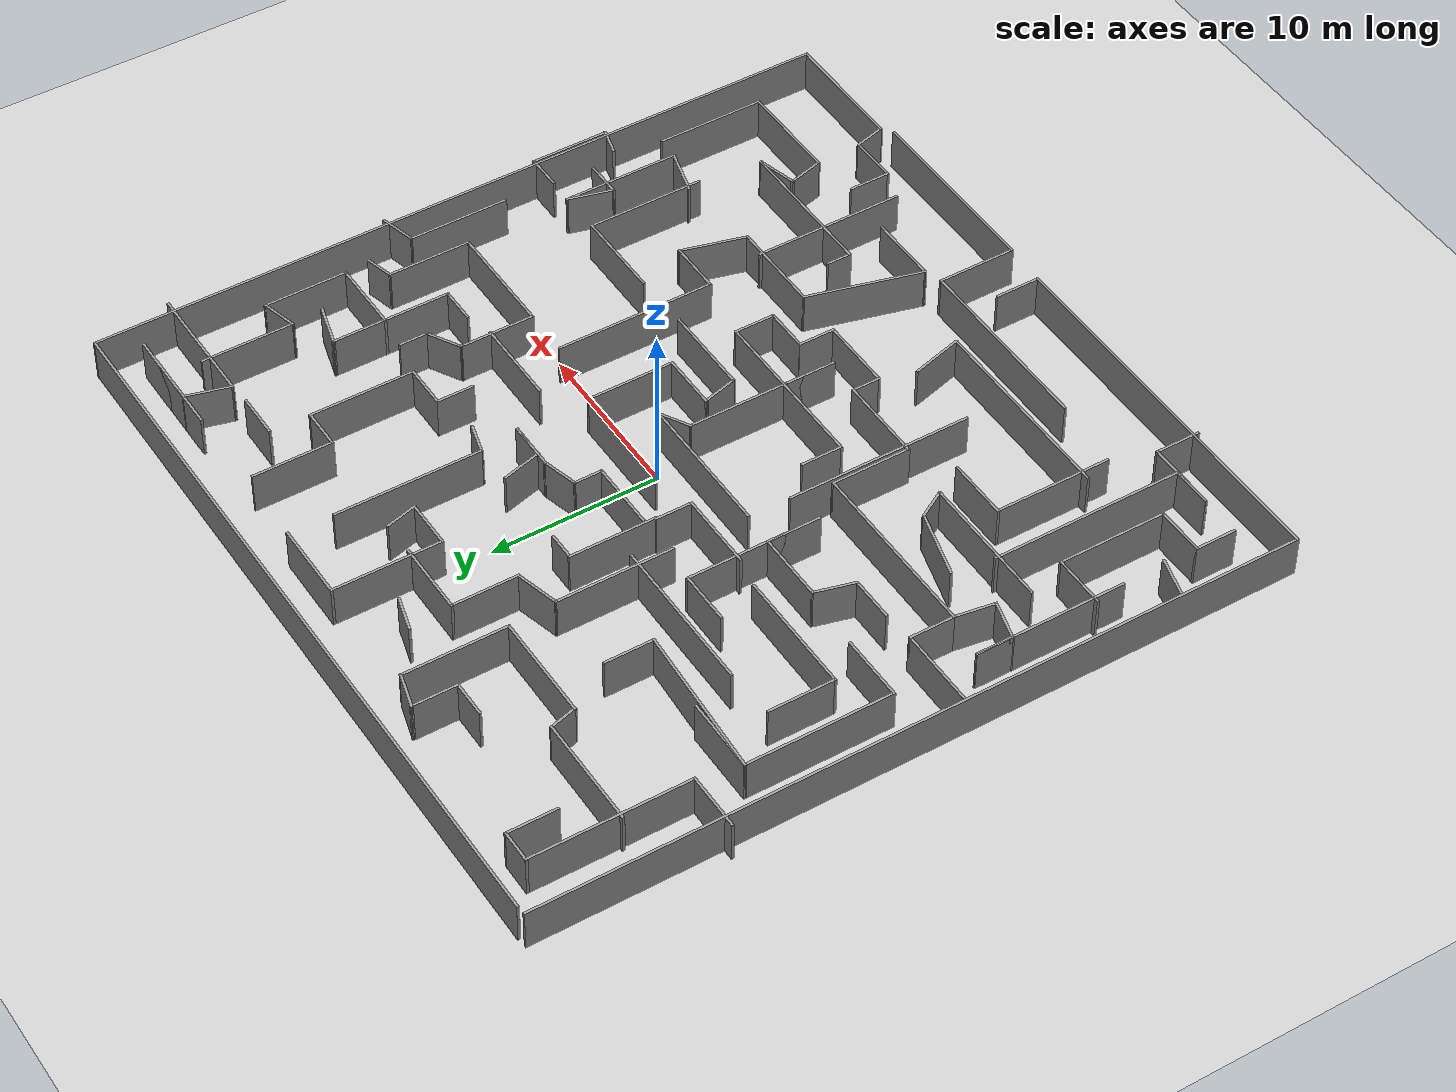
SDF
<sdf version="1.7">
 <world name="default">
  <light name="sun" type="directional">
   <pose>0 0 10 0 -0 0</pose>
   <diffuse>0.8 0.8 0.8 1</diffuse>
   <specular>0.2 0.2 0.2 1</specular>
   <attenuation>
    <range>1000</range>
    <constant>0.9</constant>
    <linear>0.01</linear>
    <quadratic>0.001</quadratic>
   </attenuation>
   <direction>-0.5 0.1 -0.9</direction>
   <spot><inner_angle>0</inner_angle><outer_angle>0</outer_angle><falloff>0</falloff></spot>
  </light>
  <model name="ground_plane">
   <static>1</static>
   <link name="link">
    <collision name="collision">
     <geometry><plane><normal>0 0 1</normal><size>100 100</size></plane></geometry>
     <surface>
      <contact><collide_bitmask>65535</collide_bitmask></contact>
      <friction><ode><mu>100</mu><mu2>50</mu2></ode></friction>
     </surface>
    </collision>
    <visual name="visual">
     <cast_shadows>0</cast_shadows>
     <geometry><plane><normal>0 0 1</normal><size>100 100</size></plane></geometry>
     <material>
      <script><uri>file://media/materials/scripts/gazebo.material</uri><name>Gazebo/Grey</name></script>
     </material>
    </visual>
   </link>
  </model>
  <gravity>0 0 -9.8</gravity>
  <magnetic_field>6e-06 2.3e-05 -4.2e-05</magnetic_field>
  <atmosphere type="adiabatic"/>
  <physics type="ode">
   <max_step_size>0.001</max_step_size>
   <real_time_factor>1</real_time_factor>
   <real_time_update_rate>1000</real_time_update_rate>
  </physics>
  <scene><ambient>0.4 0.4 0.4 1</ambient><background>0.7 0.7 0.7 1</background><shadows>1</shadows></scene>
  <spherical_coordinates>
   <surface_model>EARTH_WGS84</surface_model>
   <latitude_deg>0</latitude_deg>
   <longitude_deg>0</longitude_deg>
   <elevation>0</elevation>
   <heading_deg>0</heading_deg>
  </spherical_coordinates>
  <model name="Untitled">
   <pose>-0.253478 -1.44353 0 0 -0 0</pose>
   <link name="Wall_0">
    <collision name="Wall_0_Collision">
     <geometry><box><size>45.25 0.15 2.5</size></box></geometry>
     <pose>0 0 1.25 0 -0 0</pose>
    </collision>
    <visual name="Wall_0_Visual">
     <pose>0 0 1.25 0 -0 0</pose>
     <geometry><box><size>45.25 0.15 2.5</size></box></geometry>
     <material>
      <script><uri>file://media/materials/scripts/gazebo.material</uri><name>Gazebo/Grey</name></script>
      <ambient>1 1 1 1</ambient>
     </material>
     <meta><layer>0</layer></meta>
    </visual>
    <pose>-22.4189 0.095442 0 0 -0 -1.5708</pose>
   </link>
   <link name="Wall_1">
    <collision name="Wall_1_Collision">
     <geometry><box><size>22.75 0.15 2.5</size></box></geometry>
     <pose>0 0 1.25 0 -0 0</pose>
    </collision>
    <visual name="Wall_1_Visual">
     <pose>0 0 1.25 0 -0 0</pose>
     <geometry><box><size>22.75 0.15 2.5</size></box></geometry>
     <material>
      <script><uri>file://media/materials/scripts/gazebo.material</uri><name>Gazebo/Grey</name></script>
      <ambient>1 1 1 1</ambient>
     </material>
     <meta><layer>0</layer></meta>
    </visual>
    <pose>-11.1189 -22.4546 0 0 -0 0</pose>
   </link>
   <link name="Wall_10">
    <collision name="Wall_10_Collision">
     <geometry><box><size>5.25 0.15 2.5</size></box></geometry>
     <pose>0 0 1.25 0 -0 0</pose>
    </collision>
    <visual name="Wall_10_Visual">
     <pose>0 0 1.25 0 -0 0</pose>
     <geometry><box><size>5.25 0.15 2.5</size></box></geometry>
     <material>
      <script><uri>file://media/materials/scripts/gazebo.material</uri><name>Gazebo/Grey</name></script>
      <ambient>1 1 1 1</ambient>
     </material>
     <meta><layer>0</layer></meta>
    </visual>
    <pose>-4.23172 -9.35225 0 0 -0 0</pose>
   </link>
   <link name="Wall_100">
    <collision name="Wall_100_Collision">
     <geometry><box><size>2.25 0.15 2.5</size></box></geometry>
     <pose>0 0 1.25 0 -0 0</pose>
    </collision>
    <visual name="Wall_100_Visual">
     <pose>0 0 1.25 0 -0 0</pose>
     <geometry><box><size>2.25 0.15 2.5</size></box></geometry>
     <material>
      <script><uri>file://media/materials/scripts/gazebo.material</uri><name>Gazebo/Grey</name></script>
      <ambient>1 1 1 1</ambient>
     </material>
     <meta><layer>0</layer></meta>
    </visual>
    <pose>1.22343 6.73772 0 0 -0 0.261799</pose>
   </link>
   <link name="Wall_101">
    <collision name="Wall_101_Collision">
     <geometry><box><size>3 0.15 2.5</size></box></geometry>
     <pose>0 0 1.25 0 -0 0</pose>
    </collision>
    <visual name="Wall_101_Visual">
     <pose>0 0 1.25 0 -0 0</pose>
     <geometry><box><size>3 0.15 2.5</size></box></geometry>
     <material>
      <script><uri>file://media/materials/scripts/gazebo.material</uri><name>Gazebo/Grey</name></script>
      <ambient>1 1 1 1</ambient>
     </material>
     <meta><layer>0</layer></meta>
    </visual>
    <pose>3.66266 7.00948 0 0 -0 0</pose>
   </link>
   <link name="Wall_102">
    <collision name="Wall_102_Collision">
     <geometry><box><size>2.25 0.15 2.5</size></box></geometry>
     <pose>0 0 1.25 0 -0 0</pose>
    </collision>
    <visual name="Wall_102_Visual">
     <pose>0 0 1.25 0 -0 0</pose>
     <geometry><box><size>2.25 0.15 2.5</size></box></geometry>
     <material>
      <script><uri>file://media/materials/scripts/gazebo.material</uri><name>Gazebo/Grey</name></script>
      <ambient>1 1 1 1</ambient>
     </material>
     <meta><layer>0</layer></meta>
    </visual>
    <pose>4.03766 7.00948 0 0 -0 3.14159</pose>
   </link>
   <link name="Wall_103">
    <collision name="Wall_103_Collision">
     <geometry><box><size>2.5 0.15 2.5</size></box></geometry>
     <pose>0 0 1.25 0 -0 0</pose>
    </collision>
    <visual name="Wall_103_Visual">
     <pose>0 0 1.25 0 -0 0</pose>
     <geometry><box><size>2.5 0.15 2.5</size></box></geometry>
     <material>
      <script><uri>file://media/materials/scripts/gazebo.material</uri><name>Gazebo/Grey</name></script>
      <ambient>1 1 1 1</ambient>
     </material>
     <meta><layer>0</layer></meta>
    </visual>
    <pose>2.68354 8.14444 0 0 -0 1.8326</pose>
   </link>
   <link name="Wall_105">
    <collision name="Wall_105_Collision">
     <geometry><box><size>7.5 0.15 2.5</size></box></geometry>
     <pose>0 0 1.25 0 -0 0</pose>
    </collision>
    <visual name="Wall_105_Visual">
     <pose>0 0 1.25 0 -0 0</pose>
     <geometry><box><size>7.5 0.15 2.5</size></box></geometry>
     <material>
      <script><uri>file://media/materials/scripts/gazebo.material</uri><name>Gazebo/Grey</name></script>
      <ambient>1 1 1 1</ambient>
     </material>
     <meta><layer>0</layer></meta>
    </visual>
    <pose>-14.3033 2.52656 0 0 -0 3.14159</pose>
   </link>
   <link name="Wall_106">
    <collision name="Wall_106_Collision">
     <geometry><box><size>4 0.15 2.5</size></box></geometry>
     <pose>0 0 1.25 0 -0 0</pose>
    </collision>
    <visual name="Wall_106_Visual">
     <pose>0 0 1.25 0 -0 0</pose>
     <geometry><box><size>4 0.15 2.5</size></box></geometry>
     <material>
      <script><uri>file://media/materials/scripts/gazebo.material</uri><name>Gazebo/Grey</name></script>
      <ambient>1 1 1 1</ambient>
     </material>
     <meta><layer>0</layer></meta>
    </visual>
    <pose>-17.9783 4.45156 0 0 -0 1.5708</pose>
   </link>
   <link name="Wall_108">
    <collision name="Wall_108_Collision">
     <geometry><box><size>5.25 0.15 2.5</size></box></geometry>
     <pose>0 0 1.25 0 -0 0</pose>
    </collision>
    <visual name="Wall_108_Visual">
     <pose>0 0 1.25 0 -0 0</pose>
     <geometry><box><size>5.25 0.15 2.5</size></box></geometry>
     <material>
      <script><uri>file://media/materials/scripts/gazebo.material</uri><name>Gazebo/Grey</name></script>
      <ambient>1 1 1 1</ambient>
     </material>
     <meta><layer>0</layer></meta>
    </visual>
    <pose>9.51405 4.58523 0 0 -0 0</pose>
   </link>
   <link name="Wall_11">
    <collision name="Wall_11_Collision">
     <geometry><box><size>1.75 0.15 2.5</size></box></geometry>
     <pose>0 0 1.25 0 -0 0</pose>
    </collision>
    <visual name="Wall_11_Visual">
     <pose>0 0 1.25 0 -0 0</pose>
     <geometry><box><size>1.75 0.15 2.5</size></box></geometry>
     <material>
      <script><uri>file://media/materials/scripts/gazebo.material</uri><name>Gazebo/Grey</name></script>
      <ambient>1 1 1 1</ambient>
     </material>
     <meta><layer>0</layer></meta>
    </visual>
    <pose>-1.68172 -10.1523 0 0 -0 -1.5708</pose>
   </link>
   <link name="Wall_110">
    <collision name="Wall_110_Collision">
     <geometry><box><size>4.75 0.15 2.5</size></box></geometry>
     <pose>0 0 1.25 0 -0 0</pose>
    </collision>
    <visual name="Wall_110_Visual">
     <pose>0 0 1.25 0 -0 0</pose>
     <geometry><box><size>4.75 0.15 2.5</size></box></geometry>
     <material>
      <script><uri>file://media/materials/scripts/gazebo.material</uri><name>Gazebo/Grey</name></script>
      <ambient>1 1 1 1</ambient>
     </material>
     <meta><layer>0</layer></meta>
    </visual>
    <pose>2.5118 20.5868 0 0 -0 3.14159</pose>
   </link>
   <link name="Wall_111">
    <collision name="Wall_111_Collision">
     <geometry><box><size>6.5 0.15 2.5</size></box></geometry>
     <pose>0 0 1.25 0 -0 0</pose>
    </collision>
    <visual name="Wall_111_Visual">
     <pose>0 0 1.25 0 -0 0</pose>
     <geometry><box><size>6.5 0.15 2.5</size></box></geometry>
     <material>
      <script><uri>file://media/materials/scripts/gazebo.material</uri><name>Gazebo/Grey</name></script>
      <ambient>1 1 1 1</ambient>
     </material>
     <meta><layer>0</layer></meta>
    </visual>
    <pose>0.211799 17.4118 0 0 -0 -1.5708</pose>
   </link>
   <link name="Wall_112">
    <collision name="Wall_112_Collision">
     <geometry><box><size>3 0.15 2.5</size></box></geometry>
     <pose>0 0 1.25 0 -0 0</pose>
    </collision>
    <visual name="Wall_112_Visual">
     <pose>0 0 1.25 0 -0 0</pose>
     <geometry><box><size>3 0.15 2.5</size></box></geometry>
     <material>
      <script><uri>file://media/materials/scripts/gazebo.material</uri><name>Gazebo/Grey</name></script>
      <ambient>1 1 1 1</ambient>
     </material>
     <meta><layer>0</layer></meta>
    </visual>
    <pose>1.6368 14.2368 0 0 -0 0</pose>
   </link>
   <link name="Wall_113">
    <collision name="Wall_113_Collision">
     <geometry><box><size>2 0.15 2.5</size></box></geometry>
     <pose>0 0 1.25 0 -0 0</pose>
    </collision>
    <visual name="Wall_113_Visual">
     <pose>0 0 1.25 0 -0 0</pose>
     <geometry><box><size>2 0.15 2.5</size></box></geometry>
     <material>
      <script><uri>file://media/materials/scripts/gazebo.material</uri><name>Gazebo/Grey</name></script>
      <ambient>1 1 1 1</ambient>
     </material>
     <meta><layer>0</layer></meta>
    </visual>
    <pose>2.82239 15.1302 0 0 -0 1.8326</pose>
   </link>
   <link name="Wall_115">
    <collision name="Wall_115_Collision">
     <geometry><box><size>44.4115 0.15 2.5</size></box></geometry>
     <pose>0 0 1.25 0 -0 0</pose>
    </collision>
    <visual name="Wall_115_Visual">
     <pose>0 0 1.25 0 -0 0</pose>
     <geometry><box><size>44.4115 0.15 2.5</size></box></geometry>
     <material>
      <script><uri>file://media/materials/scripts/gazebo.material</uri><name>Gazebo/Grey</name></script>
      <ambient>1 1 1 1</ambient>
     </material>
     <meta><layer>0</layer></meta>
    </visual>
    <pose>0.273353 22.739 0 0 -0 0</pose>
   </link>
   <link name="Wall_117">
    <collision name="Wall_117_Collision">
     <geometry><box><size>2.75 0.15 2.5</size></box></geometry>
     <pose>0 0 1.25 0 -0 0</pose>
    </collision>
    <visual name="Wall_117_Visual">
     <pose>0 0 1.25 0 -0 0</pose>
     <geometry><box><size>2.75 0.15 2.5</size></box></geometry>
     <material>
      <script><uri>file://media/materials/scripts/gazebo.material</uri><name>Gazebo/Grey</name></script>
      <ambient>1 1 1 1</ambient>
     </material>
     <meta><layer>0</layer></meta>
    </visual>
    <pose>13.0566 17.9666 0 0 -0 3.14159</pose>
   </link>
   <link name="Wall_119">
    <collision name="Wall_119_Collision">
     <geometry><box><size>2.25 0.15 2.5</size></box></geometry>
     <pose>0 0 1.25 0 -0 0</pose>
    </collision>
    <visual name="Wall_119_Visual">
     <pose>0 0 1.25 0 -0 0</pose>
     <geometry><box><size>2.25 0.15 2.5</size></box></geometry>
     <material>
      <script><uri>file://media/materials/scripts/gazebo.material</uri><name>Gazebo/Grey</name></script>
      <ambient>1 1 1 1</ambient>
     </material>
     <meta><layer>0</layer></meta>
    </visual>
    <pose>-3.06372 18.2563 0 0 -0 -0.261799</pose>
   </link>
   <link name="Wall_12">
    <collision name="Wall_12_Collision">
     <geometry><box><size>4.5 0.15 2.5</size></box></geometry>
     <pose>0 0 1.25 0 -0 0</pose>
    </collision>
    <visual name="Wall_12_Visual">
     <pose>0 0 1.25 0 -0 0</pose>
     <geometry><box><size>4.5 0.15 2.5</size></box></geometry>
     <material>
      <script><uri>file://media/materials/scripts/gazebo.material</uri><name>Gazebo/Grey</name></script>
      <ambient>1 1 1 1</ambient>
     </material>
     <meta><layer>0</layer></meta>
    </visual>
    <pose>0.493275 -10.9523 0 0 -0 0</pose>
   </link>
   <link name="Wall_121">
    <collision name="Wall_121_Collision">
     <geometry><box><size>9 0.15 2.5</size></box></geometry>
     <pose>0 0 1.25 0 -0 0</pose>
    </collision>
    <visual name="Wall_121_Visual">
     <pose>0 0 1.25 0 -0 0</pose>
     <geometry><box><size>9 0.15 2.5</size></box></geometry>
     <material>
      <script><uri>file://media/materials/scripts/gazebo.material</uri><name>Gazebo/Grey</name></script>
      <ambient>1 1 1 1</ambient>
     </material>
     <meta><layer>0</layer></meta>
    </visual>
    <pose>-20.2666 -8.76925 0 0 -0 1.5708</pose>
   </link>
   <link name="Wall_122">
    <collision name="Wall_122_Collision">
     <geometry><box><size>2.25 0.15 2.5</size></box></geometry>
     <pose>0 0 1.25 0 -0 0</pose>
    </collision>
    <visual name="Wall_122_Visual">
     <pose>0 0 1.25 0 -0 0</pose>
     <geometry><box><size>2.25 0.15 2.5</size></box></geometry>
     <material>
      <script><uri>file://media/materials/scripts/gazebo.material</uri><name>Gazebo/Grey</name></script>
      <ambient>1 1 1 1</ambient>
     </material>
     <meta><layer>0</layer></meta>
    </visual>
    <pose>-20.2666 -5.39425 0 0 -0 -1.5708</pose>
   </link>
   <link name="Wall_123">
    <collision name="Wall_123_Collision">
     <geometry><box><size>2.5 0.15 2.5</size></box></geometry>
     <pose>0 0 1.25 0 -0 0</pose>
    </collision>
    <visual name="Wall_123_Visual">
     <pose>0 0 1.25 0 -0 0</pose>
     <geometry><box><size>2.5 0.15 2.5</size></box></geometry>
     <material>
      <script><uri>file://media/materials/scripts/gazebo.material</uri><name>Gazebo/Grey</name></script>
      <ambient>1 1 1 1</ambient>
     </material>
     <meta><layer>0</layer></meta>
    </visual>
    <pose>-19.1317 -6.74836 0 0 -0 -0.261799</pose>
   </link>
   <link name="Wall_124">
    <collision name="Wall_124_Collision">
     <geometry><box><size>2.47899 0.15 2.5</size></box></geometry>
     <pose>0 0 1.25 0 -0 0</pose>
    </collision>
    <visual name="Wall_124_Visual">
     <pose>0 0 1.25 0 -0 0</pose>
     <geometry><box><size>2.47899 0.15 2.5</size></box></geometry>
     <material>
      <script><uri>file://media/materials/scripts/gazebo.material</uri><name>Gazebo/Grey</name></script>
      <ambient>1 1 1 1</ambient>
     </material>
     <meta><layer>0</layer></meta>
    </visual>
    <pose>-17.8142 -5.90236 0 0 -0 1.41344</pose>
   </link>
   <link name="Wall_126">
    <collision name="Wall_126_Collision">
     <geometry><box><size>2.5 0.15 2.5</size></box></geometry>
     <pose>0 0 1.25 0 -0 0</pose>
    </collision>
    <visual name="Wall_126_Visual">
     <pose>0 0 1.25 0 -0 0</pose>
     <geometry><box><size>2.5 0.15 2.5</size></box></geometry>
     <material>
      <script><uri>file://media/materials/scripts/gazebo.material</uri><name>Gazebo/Grey</name></script>
      <ambient>1 1 1 1</ambient>
     </material>
     <meta><layer>0</layer></meta>
    </visual>
    <pose>-21.1903 -15.557 0 0 -0 -0.261799</pose>
   </link>
   <link name="Wall_128">
    <collision name="Wall_128_Collision">
     <geometry><box><size>2.5 0.15 2.5</size></box></geometry>
     <pose>0 0 1.25 0 -0 0</pose>
    </collision>
    <visual name="Wall_128_Visual">
     <pose>0 0 1.25 0 -0 0</pose>
     <geometry><box><size>2.5 0.15 2.5</size></box></geometry>
     <material>
      <script><uri>file://media/materials/scripts/gazebo.material</uri><name>Gazebo/Grey</name></script>
      <ambient>1 1 1 1</ambient>
     </material>
     <meta><layer>0</layer></meta>
    </visual>
    <pose>-20.2666 -18.9439 0 0 -0 1.5708</pose>
   </link>
   <link name="Wall_129">
    <collision name="Wall_129_Collision">
     <geometry><box><size>3 0.15 2.5</size></box></geometry>
     <pose>0 0 1.25 0 -0 0</pose>
    </collision>
    <visual name="Wall_129_Visual">
     <pose>0 0 1.25 0 -0 0</pose>
     <geometry><box><size>3 0.15 2.5</size></box></geometry>
     <material>
      <script><uri>file://media/materials/scripts/gazebo.material</uri><name>Gazebo/Grey</name></script>
      <ambient>1 1 1 1</ambient>
     </material>
     <meta><layer>0</layer></meta>
    </visual>
    <pose>-18.8416 -17.7689 0 0 -0 0</pose>
   </link>
   <link name="Wall_13">
    <collision name="Wall_13_Collision">
     <geometry><box><size>2.25 0.15 2.5</size></box></geometry>
     <pose>0 0 1.25 0 -0 0</pose>
    </collision>
    <visual name="Wall_13_Visual">
     <pose>0 0 1.25 0 -0 0</pose>
     <geometry><box><size>2.25 0.15 2.5</size></box></geometry>
     <material>
      <script><uri>file://media/materials/scripts/gazebo.material</uri><name>Gazebo/Grey</name></script>
      <ambient>1 1 1 1</ambient>
     </material>
     <meta><layer>0</layer></meta>
    </visual>
    <pose>2.66827 -9.90225 0 0 -0 1.5708</pose>
   </link>
   <link name="Wall_130">
    <collision name="Wall_130_Collision">
     <geometry><box><size>6.5 0.15 2.5</size></box></geometry>
     <pose>0 0 1.25 0 -0 0</pose>
    </collision>
    <visual name="Wall_130_Visual">
     <pose>0 0 1.25 0 -0 0</pose>
     <geometry><box><size>6.5 0.15 2.5</size></box></geometry>
     <material>
      <script><uri>file://media/materials/scripts/gazebo.material</uri><name>Gazebo/Grey</name></script>
      <ambient>1 1 1 1</ambient>
     </material>
     <meta><layer>0</layer></meta>
    </visual>
    <pose>-17.4166 -14.5939 0 0 -0 1.5708</pose>
   </link>
   <link name="Wall_131">
    <collision name="Wall_131_Collision">
     <geometry><box><size>3.25 0.15 2.5</size></box></geometry>
     <pose>0 0 1.25 0 -0 0</pose>
    </collision>
    <visual name="Wall_131_Visual">
     <pose>0 0 1.25 0 -0 0</pose>
     <geometry><box><size>3.25 0.15 2.5</size></box></geometry>
     <material>
      <script><uri>file://media/materials/scripts/gazebo.material</uri><name>Gazebo/Grey</name></script>
      <ambient>1 1 1 1</ambient>
     </material>
     <meta><layer>0</layer></meta>
    </visual>
    <pose>-18.9666 -11.4189 0 0 -0 3.14159</pose>
   </link>
   <link name="Wall_133">
    <collision name="Wall_133_Collision">
     <geometry><box><size>2.75 0.15 2.5</size></box></geometry>
     <pose>0 0 1.25 0 -0 0</pose>
    </collision>
    <visual name="Wall_133_Visual">
     <pose>0 0 1.25 0 -0 0</pose>
     <geometry><box><size>2.75 0.15 2.5</size></box></geometry>
     <material>
      <script><uri>file://media/materials/scripts/gazebo.material</uri><name>Gazebo/Grey</name></script>
      <ambient>1 1 1 1</ambient>
     </material>
     <meta><layer>0</layer></meta>
    </visual>
    <pose>-13.7163 -21.439 0 0 -0 1.5708</pose>
   </link>
   <link name="Wall_134">
    <collision name="Wall_134_Collision">
     <geometry><box><size>4.25 0.15 2.5</size></box></geometry>
     <pose>0 0 1.25 0 -0 0</pose>
    </collision>
    <visual name="Wall_134_Visual">
     <pose>0 0 1.25 0 -0 0</pose>
     <geometry><box><size>4.25 0.15 2.5</size></box></geometry>
     <material>
      <script><uri>file://media/materials/scripts/gazebo.material</uri><name>Gazebo/Grey</name></script>
      <ambient>1 1 1 1</ambient>
     </material>
     <meta><layer>0</layer></meta>
    </visual>
    <pose>-15.7663 -20.139 0 0 -0 3.14159</pose>
   </link>
   <link name="Wall_135">
    <collision name="Wall_135_Collision">
     <geometry><box><size>2.5 0.15 2.5</size></box></geometry>
     <pose>0 0 1.25 0 -0 0</pose>
    </collision>
    <visual name="Wall_135_Visual">
     <pose>0 0 1.25 0 -0 0</pose>
     <geometry><box><size>2.5 0.15 2.5</size></box></geometry>
     <material>
      <script><uri>file://media/materials/scripts/gazebo.material</uri><name>Gazebo/Grey</name></script>
      <ambient>1 1 1 1</ambient>
     </material>
     <meta><layer>0</layer></meta>
    </visual>
    <pose>-16.6413 -20.139 0 0 -0 0</pose>
   </link>
   <link name="Wall_136">
    <collision name="Wall_136_Collision">
     <geometry><box><size>11.5 0.15 2.5</size></box></geometry>
     <pose>0 0 1.25 0 -0 0</pose>
    </collision>
    <visual name="Wall_136_Visual">
     <pose>0 0 1.25 0 -0 0</pose>
     <geometry><box><size>11.5 0.15 2.5</size></box></geometry>
     <material>
      <script><uri>file://media/materials/scripts/gazebo.material</uri><name>Gazebo/Grey</name></script>
      <ambient>1 1 1 1</ambient>
     </material>
     <meta><layer>0</layer></meta>
    </visual>
    <pose>-15.4663 -14.464 0 0 -0 1.5708</pose>
   </link>
   <link name="Wall_138">
    <collision name="Wall_138_Collision">
     <geometry><box><size>11.5 0.15 2.5</size></box></geometry>
     <pose>0 0 1.25 0 -0 0</pose>
    </collision>
    <visual name="Wall_138_Visual">
     <pose>0 0 1.25 0 -0 0</pose>
     <geometry><box><size>11.5 0.15 2.5</size></box></geometry>
     <material>
      <script><uri>file://media/materials/scripts/gazebo.material</uri><name>Gazebo/Grey</name></script>
      <ambient>1 1 1 1</ambient>
     </material>
     <meta><layer>0</layer></meta>
    </visual>
    <pose>-2.8946 -17.9666 0 0 -0 0</pose>
   </link>
   <link name="Wall_139">
    <collision name="Wall_139_Collision">
     <geometry><box><size>4.75 0.15 2.5</size></box></geometry>
     <pose>0 0 1.25 0 -0 0</pose>
    </collision>
    <visual name="Wall_139_Visual">
     <pose>0 0 1.25 0 -0 0</pose>
     <geometry><box><size>4.75 0.15 2.5</size></box></geometry>
     <material>
      <script><uri>file://media/materials/scripts/gazebo.material</uri><name>Gazebo/Grey</name></script>
      <ambient>1 1 1 1</ambient>
     </material>
     <meta><layer>0</layer></meta>
    </visual>
    <pose>2.7804 -20.2666 0 0 -0 -1.5708</pose>
   </link>
   <link name="Wall_14">
    <collision name="Wall_14_Collision">
     <geometry><box><size>2.75 0.15 2.5</size></box></geometry>
     <pose>0 0 1.25 0 -0 0</pose>
    </collision>
    <visual name="Wall_14_Visual">
     <pose>0 0 1.25 0 -0 0</pose>
     <geometry><box><size>2.75 0.15 2.5</size></box></geometry>
     <material>
      <script><uri>file://media/materials/scripts/gazebo.material</uri><name>Gazebo/Grey</name></script>
      <ambient>1 1 1 1</ambient>
     </material>
     <meta><layer>0</layer></meta>
    </visual>
    <pose>3.96828 -8.85225 0 0 -0 0</pose>
   </link>
   <link name="Wall_140">
    <collision name="Wall_140_Collision">
     <geometry><box><size>11.5 0.15 2.5</size></box></geometry>
     <pose>0 0 1.25 0 -0 0</pose>
    </collision>
    <visual name="Wall_140_Visual">
     <pose>0 0 1.25 0 -0 0</pose>
     <geometry><box><size>11.5 0.15 2.5</size></box></geometry>
     <material>
      <script><uri>file://media/materials/scripts/gazebo.material</uri><name>Gazebo/Grey</name></script>
      <ambient>1 1 1 1</ambient>
     </material>
     <meta><layer>0</layer></meta>
    </visual>
    <pose>8.4554 -22.5666 0 0 -0 0</pose>
   </link>
   <link name="Wall_142">
    <collision name="Wall_142_Collision">
     <geometry><box><size>2.75 0.15 2.5</size></box></geometry>
     <pose>0 0 1.25 0 -0 0</pose>
    </collision>
    <visual name="Wall_142_Visual">
     <pose>0 0 1.25 0 -0 0</pose>
     <geometry><box><size>2.75 0.15 2.5</size></box></geometry>
     <material>
      <script><uri>file://media/materials/scripts/gazebo.material</uri><name>Gazebo/Grey</name></script>
      <ambient>1 1 1 1</ambient>
     </material>
     <meta><layer>0</layer></meta>
    </visual>
    <pose>-14.475 -1.9651 0 0 -0 0</pose>
   </link>
   <link name="Wall_143">
    <collision name="Wall_143_Collision">
     <geometry><box><size>2.5 0.15 2.5</size></box></geometry>
     <pose>0 0 1.25 0 -0 0</pose>
    </collision>
    <visual name="Wall_143_Visual">
     <pose>0 0 1.25 0 -0 0</pose>
     <geometry><box><size>2.5 0.15 2.5</size></box></geometry>
     <material>
      <script><uri>file://media/materials/scripts/gazebo.material</uri><name>Gazebo/Grey</name></script>
      <ambient>1 1 1 1</ambient>
     </material>
     <meta><layer>0</layer></meta>
    </visual>
    <pose>-12.8709 -0.830138 0 0 -0 1.309</pose>
   </link>
   <link name="Wall_144">
    <collision name="Wall_144_Collision">
     <geometry><box><size>4.25 0.15 2.5</size></box></geometry>
     <pose>0 0 1.25 0 -0 0</pose>
    </collision>
    <visual name="Wall_144_Visual">
     <pose>0 0 1.25 0 -0 0</pose>
     <geometry><box><size>4.25 0.15 2.5</size></box></geometry>
     <material>
      <script><uri>file://media/materials/scripts/gazebo.material</uri><name>Gazebo/Grey</name></script>
      <ambient>1 1 1 1</ambient>
     </material>
     <meta><layer>0</layer></meta>
    </visual>
    <pose>-10.5167 0.304825 0 0 -0 0</pose>
   </link>
   <link name="Wall_145">
    <collision name="Wall_145_Collision">
     <geometry><box><size>3.25 0.15 2.5</size></box></geometry>
     <pose>0 0 1.25 0 -0 0</pose>
    </collision>
    <visual name="Wall_145_Visual">
     <pose>0 0 1.25 0 -0 0</pose>
     <geometry><box><size>3.25 0.15 2.5</size></box></geometry>
     <material>
      <script><uri>file://media/materials/scripts/gazebo.material</uri><name>Gazebo/Grey</name></script>
      <ambient>1 1 1 1</ambient>
     </material>
     <meta><layer>0</layer></meta>
    </visual>
    <pose>-8.46674 -1.24517 0 0 -0 -1.5708</pose>
   </link>
   <link name="Wall_146">
    <collision name="Wall_146_Collision">
     <geometry><box><size>8 0.15 2.5</size></box></geometry>
     <pose>0 0 1.25 0 -0 0</pose>
    </collision>
    <visual name="Wall_146_Visual">
     <pose>0 0 1.25 0 -0 0</pose>
     <geometry><box><size>8 0.15 2.5</size></box></geometry>
     <material>
      <script><uri>file://media/materials/scripts/gazebo.material</uri><name>Gazebo/Grey</name></script>
      <ambient>1 1 1 1</ambient>
     </material>
     <meta><layer>0</layer></meta>
    </visual>
    <pose>-8.46674 1.12983 0 0 -0 1.5708</pose>
   </link>
   <link name="Wall_147">
    <collision name="Wall_147_Collision">
     <geometry><box><size>3.25 0.15 2.5</size></box></geometry>
     <pose>0 0 1.25 0 -0 0</pose>
    </collision>
    <visual name="Wall_147_Visual">
     <pose>0 0 1.25 0 -0 0</pose>
     <geometry><box><size>3.25 0.15 2.5</size></box></geometry>
     <material>
      <script><uri>file://media/materials/scripts/gazebo.material</uri><name>Gazebo/Grey</name></script>
      <ambient>1 1 1 1</ambient>
     </material>
     <meta><layer>0</layer></meta>
    </visual>
    <pose>-10.0167 5.05482 0 0 -0 3.14159</pose>
   </link>
   <link name="Wall_149">
    <collision name="Wall_149_Collision">
     <geometry><box><size>4.75 0.15 2.5</size></box></geometry>
     <pose>0 0 1.25 0 -0 0</pose>
    </collision>
    <visual name="Wall_149_Visual">
     <pose>0 0 1.25 0 -0 0</pose>
     <geometry><box><size>4.75 0.15 2.5</size></box></geometry>
     <material>
      <script><uri>file://media/materials/scripts/gazebo.material</uri><name>Gazebo/Grey</name></script>
      <ambient>1 1 1 1</ambient>
     </material>
     <meta><layer>0</layer></meta>
    </visual>
    <pose>-6.45675 2.15225 0 0 -0 0</pose>
   </link>
   <link name="Wall_15">
    <collision name="Wall_15_Collision">
     <geometry><box><size>2.5 0.15 2.5</size></box></geometry>
     <pose>0 0 1.25 0 -0 0</pose>
    </collision>
    <visual name="Wall_15_Visual">
     <pose>0 0 1.25 0 -0 0</pose>
     <geometry><box><size>2.5 0.15 2.5</size></box></geometry>
     <material>
      <script><uri>file://media/materials/scripts/gazebo.material</uri><name>Gazebo/Grey</name></script>
      <ambient>1 1 1 1</ambient>
     </material>
     <meta><layer>0</layer></meta>
    </visual>
    <pose>5.26828 -7.67725 0 0 -0 1.5708</pose>
   </link>
   <link name="Wall_150">
    <collision name="Wall_150_Collision">
     <geometry><box><size>2.25 0.15 2.5</size></box></geometry>
     <pose>0 0 1.25 0 -0 0</pose>
    </collision>
    <visual name="Wall_150_Visual">
     <pose>0 0 1.25 0 -0 0</pose>
     <geometry><box><size>2.25 0.15 2.5</size></box></geometry>
     <material>
      <script><uri>file://media/materials/scripts/gazebo.material</uri><name>Gazebo/Grey</name></script>
      <ambient>1 1 1 1</ambient>
     </material>
     <meta><layer>0</layer></meta>
    </visual>
    <pose>-4.15675 3.20225 0 0 -0 1.5708</pose>
   </link>
   <link name="Wall_153">
    <collision name="Wall_153_Collision">
     <geometry><box><size>6.5 0.15 2.5</size></box></geometry>
     <pose>0 0 1.25 0 -0 0</pose>
    </collision>
    <visual name="Wall_153_Visual">
     <pose>0 0 1.25 0 -0 0</pose>
     <geometry><box><size>6.5 0.15 2.5</size></box></geometry>
     <material>
      <script><uri>file://media/materials/scripts/gazebo.material</uri><name>Gazebo/Grey</name></script>
      <ambient>1 1 1 1</ambient>
     </material>
     <meta><layer>0</layer></meta>
    </visual>
    <pose>20.3454 -14.4041 0 0 -0 -1.5708</pose>
   </link>
   <link name="Wall_154">
    <collision name="Wall_154_Collision">
     <geometry><box><size>6.25 0.15 2.5</size></box></geometry>
     <pose>0 0 1.25 0 -0 0</pose>
    </collision>
    <visual name="Wall_154_Visual">
     <pose>0 0 1.25 0 -0 0</pose>
     <geometry><box><size>6.25 0.15 2.5</size></box></geometry>
     <material>
      <script><uri>file://media/materials/scripts/gazebo.material</uri><name>Gazebo/Grey</name></script>
      <ambient>1 1 1 1</ambient>
     </material>
     <meta><layer>0</layer></meta>
    </visual>
    <pose>17.2954 -17.5791 0 0 -0 3.14159</pose>
   </link>
   <link name="Wall_155">
    <collision name="Wall_155_Collision">
     <geometry><box><size>2.25 0.15 2.5</size></box></geometry>
     <pose>0 0 1.25 0 -0 0</pose>
    </collision>
    <visual name="Wall_155_Visual">
     <pose>0 0 1.25 0 -0 0</pose>
     <geometry><box><size>2.25 0.15 2.5</size></box></geometry>
     <material>
      <script><uri>file://media/materials/scripts/gazebo.material</uri><name>Gazebo/Grey</name></script>
      <ambient>1 1 1 1</ambient>
     </material>
     <meta><layer>0</layer></meta>
    </visual>
    <pose>13.9737 -16.5649 0 0 -0 1.8326</pose>
   </link>
   <link name="Wall_156">
    <collision name="Wall_156_Collision">
     <geometry><box><size>2.5 0.15 2.5</size></box></geometry>
     <pose>0 0 1.25 0 -0 0</pose>
    </collision>
    <visual name="Wall_156_Visual">
     <pose>0 0 1.25 0 -0 0</pose>
     <geometry><box><size>2.5 0.15 2.5</size></box></geometry>
     <material>
      <script><uri>file://media/materials/scripts/gazebo.material</uri><name>Gazebo/Grey</name></script>
      <ambient>1 1 1 1</ambient>
     </material>
     <meta><layer>0</layer></meta>
    </visual>
    <pose>14.8369 -15.2466 0 0 -0 0.261799</pose>
   </link>
   <link name="Wall_157">
    <collision name="Wall_157_Collision">
     <geometry><box><size>9 0.15 2.5</size></box></geometry>
     <pose>0 0 1.25 0 -0 0</pose>
    </collision>
    <visual name="Wall_157_Visual">
     <pose>0 0 1.25 0 -0 0</pose>
     <geometry><box><size>9 0.15 2.5</size></box></geometry>
     <material>
      <script><uri>file://media/materials/scripts/gazebo.material</uri><name>Gazebo/Grey</name></script>
      <ambient>1 1 1 1</ambient>
     </material>
     <meta><layer>0</layer></meta>
    </visual>
    <pose>11.5469 -14.9425 0 0 -0 3.14159</pose>
   </link>
   <link name="Wall_158">
    <collision name="Wall_158_Collision">
     <geometry><box><size>1.5 0.15 2.5</size></box></geometry>
     <pose>0 0 1.25 0 -0 0</pose>
    </collision>
    <visual name="Wall_158_Visual">
     <pose>0 0 1.25 0 -0 0</pose>
     <geometry><box><size>1.5 0.15 2.5</size></box></geometry>
     <material>
      <script><uri>file://media/materials/scripts/gazebo.material</uri><name>Gazebo/Grey</name></script>
      <ambient>1 1 1 1</ambient>
     </material>
     <meta><layer>0</layer></meta>
    </visual>
    <pose>7.12186 -14.2675 0 0 -0 1.5708</pose>
   </link>
   <link name="Wall_16">
    <collision name="Wall_16_Collision">
     <geometry><box><size>10.25 0.15 2.5</size></box></geometry>
     <pose>0 0 1.25 0 -0 0</pose>
    </collision>
    <visual name="Wall_16_Visual">
     <pose>0 0 1.25 0 -0 0</pose>
     <geometry><box><size>10.25 0.15 2.5</size></box></geometry>
     <material>
      <script><uri>file://media/materials/scripts/gazebo.material</uri><name>Gazebo/Grey</name></script>
      <ambient>1 1 1 1</ambient>
     </material>
     <meta><layer>0</layer></meta>
    </visual>
    <pose>0.218275 -6.50225 0 0 -0 3.14159</pose>
   </link>
   <link name="Wall_160">
    <collision name="Wall_160_Collision">
     <geometry><box><size>9 0.15 2.5</size></box></geometry>
     <pose>0 0 1.25 0 -0 0</pose>
    </collision>
    <visual name="Wall_160_Visual">
     <pose>0 0 1.25 0 -0 0</pose>
     <geometry><box><size>9 0.15 2.5</size></box></geometry>
     <material>
      <script><uri>file://media/materials/scripts/gazebo.material</uri><name>Gazebo/Grey</name></script>
      <ambient>1 1 1 1</ambient>
     </material>
     <meta><layer>0</layer></meta>
    </visual>
    <pose>9.67776 -15.2798 0 0 -0 -1.5708</pose>
   </link>
   <link name="Wall_162">
    <collision name="Wall_162_Collision">
     <geometry><box><size>2.25 0.15 2.5</size></box></geometry>
     <pose>0 0 1.25 0 -0 0</pose>
    </collision>
    <visual name="Wall_162_Visual">
     <pose>0 0 1.25 0 -0 0</pose>
     <geometry><box><size>2.25 0.15 2.5</size></box></geometry>
     <material>
      <script><uri>file://media/materials/scripts/gazebo.material</uri><name>Gazebo/Grey</name></script>
      <ambient>1 1 1 1</ambient>
     </material>
     <meta><layer>0</layer></meta>
    </visual>
    <pose>21.5826 -4.30451 0 0 -0 0</pose>
   </link>
   <link name="Wall_163">
    <collision name="Wall_163_Collision">
     <geometry><box><size>4.75 0.15 2.5</size></box></geometry>
     <pose>0 0 1.25 0 -0 0</pose>
    </collision>
    <visual name="Wall_163_Visual">
     <pose>0 0 1.25 0 -0 0</pose>
     <geometry><box><size>4.75 0.15 2.5</size></box></geometry>
     <material>
      <script><uri>file://media/materials/scripts/gazebo.material</uri><name>Gazebo/Grey</name></script>
      <ambient>1 1 1 1</ambient>
     </material>
     <meta><layer>0</layer></meta>
    </visual>
    <pose>22.6326 -6.60451 0 0 -0 -1.5708</pose>
   </link>
   <link name="Wall_164">
    <collision name="Wall_164_Collision">
     <geometry><box><size>1.75 0.15 2.5</size></box></geometry>
     <pose>0 0 1.25 0 -0 0</pose>
    </collision>
    <visual name="Wall_164_Visual">
     <pose>0 0 1.25 0 -0 0</pose>
     <geometry><box><size>1.75 0.15 2.5</size></box></geometry>
     <material>
      <script><uri>file://media/materials/scripts/gazebo.material</uri><name>Gazebo/Grey</name></script>
      <ambient>1 1 1 1</ambient>
     </material>
     <meta><layer>0</layer></meta>
    </visual>
    <pose>21.8599 -8.69745 0 0 -0 2.87979</pose>
   </link>
   <link name="Wall_166">
    <collision name="Wall_166_Collision">
     <geometry><box><size>6 0.15 2.5</size></box></geometry>
     <pose>0 0 1.25 0 -0 0</pose>
    </collision>
    <visual name="Wall_166_Visual">
     <pose>0 0 1.25 0 -0 0</pose>
     <geometry><box><size>6 0.15 2.5</size></box></geometry>
     <material>
      <script><uri>file://media/materials/scripts/gazebo.material</uri><name>Gazebo/Grey</name></script>
      <ambient>1 1 1 1</ambient>
     </material>
     <meta><layer>0</layer></meta>
    </visual>
    <pose>20.7198 1.61493 0 0 -0 1.5708</pose>
   </link>
   <link name="Wall_167">
    <collision name="Wall_167_Collision">
     <geometry><box><size>2.25 0.15 2.5</size></box></geometry>
     <pose>0 0 1.25 0 -0 0</pose>
    </collision>
    <visual name="Wall_167_Visual">
     <pose>0 0 1.25 0 -0 0</pose>
     <geometry><box><size>2.25 0.15 2.5</size></box></geometry>
     <material>
      <script><uri>file://media/materials/scripts/gazebo.material</uri><name>Gazebo/Grey</name></script>
      <ambient>1 1 1 1</ambient>
     </material>
     <meta><layer>0</layer></meta>
    </visual>
    <pose>21.734 4.81169 0 0 -0 0.261799</pose>
   </link>
   <link name="Wall_17">
    <collision name="Wall_17_Collision">
     <geometry><box><size>2.5 0.15 2.5</size></box></geometry>
     <pose>0 0 1.25 0 -0 0</pose>
    </collision>
    <visual name="Wall_17_Visual">
     <pose>0 0 1.25 0 -0 0</pose>
     <geometry><box><size>2.5 0.15 2.5</size></box></geometry>
     <material>
      <script><uri>file://media/materials/scripts/gazebo.material</uri><name>Gazebo/Grey</name></script>
      <ambient>1 1 1 1</ambient>
     </material>
     <meta><layer>0</layer></meta>
    </visual>
    <pose>-4.83172 -5.32725 0 0 -0 1.5708</pose>
   </link>
   <link name="Wall_170">
    <collision name="Wall_170_Collision">
     <geometry><box><size>3 0.15 2.5</size></box></geometry>
     <pose>0 0 1.25 0 -0 0</pose>
    </collision>
    <visual name="Wall_170_Visual">
     <pose>0 0 1.25 0 -0 0</pose>
     <geometry><box><size>3 0.15 2.5</size></box></geometry>
     <material>
      <script><uri>file://media/materials/scripts/gazebo.material</uri><name>Gazebo/Grey</name></script>
      <ambient>1 1 1 1</ambient>
     </material>
     <meta><layer>0</layer></meta>
    </visual>
    <pose>17.6045 -10.7558 0 0 -0 -0.261799</pose>
   </link>
   <link name="Wall_171">
    <collision name="Wall_171_Collision">
     <geometry><box><size>7 0.15 2.5</size></box></geometry>
     <pose>0 0 1.25 0 -0 0</pose>
    </collision>
    <visual name="Wall_171_Visual">
     <pose>0 0 1.25 0 -0 0</pose>
     <geometry><box><size>7 0.15 2.5</size></box></geometry>
     <material>
      <script><uri>file://media/materials/scripts/gazebo.material</uri><name>Gazebo/Grey</name></script>
      <ambient>1 1 1 1</ambient>
     </material>
     <meta><layer>0</layer></meta>
    </visual>
    <pose>18.981 -7.69959 0 0 -0 1.5708</pose>
   </link>
   <link name="Wall_172">
    <collision name="Wall_172_Collision">
     <geometry><box><size>2.75 0.15 2.5</size></box></geometry>
     <pose>0 0 1.25 0 -0 0</pose>
    </collision>
    <visual name="Wall_172_Visual">
     <pose>0 0 1.25 0 -0 0</pose>
     <geometry><box><size>2.75 0.15 2.5</size></box></geometry>
     <material>
      <script><uri>file://media/materials/scripts/gazebo.material</uri><name>Gazebo/Grey</name></script>
      <ambient>1 1 1 1</ambient>
     </material>
     <meta><layer>0</layer></meta>
    </visual>
    <pose>18.6445 -5.5303 0 0 -0 -1.8326</pose>
   </link>
   <link name="Wall_173">
    <collision name="Wall_173_Collision">
     <geometry><box><size>2.25 0.15 2.5</size></box></geometry>
     <pose>0 0 1.25 0 -0 0</pose>
    </collision>
    <visual name="Wall_173_Visual">
     <pose>0 0 1.25 0 -0 0</pose>
     <geometry><box><size>2.25 0.15 2.5</size></box></geometry>
     <material>
      <script><uri>file://media/materials/scripts/gazebo.material</uri><name>Gazebo/Grey</name></script>
      <ambient>1 1 1 1</ambient>
     </material>
     <meta><layer>0</layer></meta>
    </visual>
    <pose>19.3581 -6.786 0 0 -0 0</pose>
   </link>
   <link name="Wall_175">
    <collision name="Wall_175_Collision">
     <geometry><box><size>5.5 0.15 2.5</size></box></geometry>
     <pose>0 0 1.25 0 -0 0</pose>
    </collision>
    <visual name="Wall_175_Visual">
     <pose>0 0 1.25 0 -0 0</pose>
     <geometry><box><size>5.5 0.15 2.5</size></box></geometry>
     <material>
      <script><uri>file://media/materials/scripts/gazebo.material</uri><name>Gazebo/Grey</name></script>
      <ambient>1 1 1 1</ambient>
     </material>
     <meta><layer>0</layer></meta>
    </visual>
    <pose>18.1932 15.8531 0 0 -0 -1.5708</pose>
   </link>
   <link name="Wall_176">
    <collision name="Wall_176_Collision">
     <geometry><box><size>2.25 0.15 2.5</size></box></geometry>
     <pose>0 0 1.25 0 -0 0</pose>
    </collision>
    <visual name="Wall_176_Visual">
     <pose>0 0 1.25 0 -0 0</pose>
     <geometry><box><size>2.25 0.15 2.5</size></box></geometry>
     <material>
      <script><uri>file://media/materials/scripts/gazebo.material</uri><name>Gazebo/Grey</name></script>
      <ambient>1 1 1 1</ambient>
     </material>
     <meta><layer>0</layer></meta>
    </visual>
    <pose>19.2074 13.4498 0 0 -0 0.261799</pose>
   </link>
   <link name="Wall_177">
    <collision name="Wall_177_Collision">
     <geometry><box><size>5 0.15 2.5</size></box></geometry>
     <pose>0 0 1.25 0 -0 0</pose>
    </collision>
    <visual name="Wall_177_Visual">
     <pose>0 0 1.25 0 -0 0</pose>
     <geometry><box><size>5 0.15 2.5</size></box></geometry>
     <material>
      <script><uri>file://media/materials/scripts/gazebo.material</uri><name>Gazebo/Grey</name></script>
      <ambient>1 1 1 1</ambient>
     </material>
     <meta><layer>0</layer></meta>
    </visual>
    <pose>20.2216 11.2966 0 0 -0 -1.5708</pose>
   </link>
   <link name="Wall_178">
    <collision name="Wall_178_Collision">
     <geometry><box><size>4.5 0.15 2.5</size></box></geometry>
     <pose>0 0 1.25 0 -0 0</pose>
    </collision>
    <visual name="Wall_178_Visual">
     <pose>0 0 1.25 0 -0 0</pose>
     <geometry><box><size>4.5 0.15 2.5</size></box></geometry>
     <material>
      <script><uri>file://media/materials/scripts/gazebo.material</uri><name>Gazebo/Grey</name></script>
      <ambient>1 1 1 1</ambient>
     </material>
     <meta><layer>0</layer></meta>
    </visual>
    <pose>18.0466 8.87161 0 0 -0 3.14159</pose>
   </link>
   <link name="Wall_179">
    <collision name="Wall_179_Collision">
     <geometry><box><size>4 0.15 2.5</size></box></geometry>
     <pose>0 0 1.25 0 -0 0</pose>
    </collision>
    <visual name="Wall_179_Visual">
     <pose>0 0 1.25 0 -0 0</pose>
     <geometry><box><size>4 0.15 2.5</size></box></geometry>
     <material>
      <script><uri>file://media/materials/scripts/gazebo.material</uri><name>Gazebo/Grey</name></script>
      <ambient>1 1 1 1</ambient>
     </material>
     <meta><layer>0</layer></meta>
    </visual>
    <pose>15.8716 6.94661 0 0 -0 -1.5708</pose>
   </link>
   <link name="Wall_180">
    <collision name="Wall_180_Collision">
     <geometry><box><size>2.25 0.15 2.5</size></box></geometry>
     <pose>0 0 1.25 0 -0 0</pose>
    </collision>
    <visual name="Wall_180_Visual">
     <pose>0 0 1.25 0 -0 0</pose>
     <geometry><box><size>2.25 0.15 2.5</size></box></geometry>
     <material>
      <script><uri>file://media/materials/scripts/gazebo.material</uri><name>Gazebo/Grey</name></script>
      <ambient>1 1 1 1</ambient>
     </material>
     <meta><layer>0</layer></meta>
    </visual>
    <pose>14.8216 5.02161 0 0 -0 3.14159</pose>
   </link>
   <link name="Wall_182">
    <collision name="Wall_182_Collision">
     <geometry><box><size>3.25 0.15 2.5</size></box></geometry>
     <pose>0 0 1.25 0 -0 0</pose>
    </collision>
    <visual name="Wall_182_Visual">
     <pose>0 0 1.25 0 -0 0</pose>
     <geometry><box><size>3.25 0.15 2.5</size></box></geometry>
     <material>
      <script><uri>file://media/materials/scripts/gazebo.material</uri><name>Gazebo/Grey</name></script>
      <ambient>1 1 1 1</ambient>
     </material>
     <meta><layer>0</layer></meta>
    </visual>
    <pose>15.8716 10.4216 0 0 -0 1.5708</pose>
   </link>
   <link name="Wall_183">
    <collision name="Wall_183_Collision">
     <geometry><box><size>2.75 0.15 2.5</size></box></geometry>
     <pose>0 0 1.25 0 -0 0</pose>
    </collision>
    <visual name="Wall_183_Visual">
     <pose>0 0 1.25 0 -0 0</pose>
     <geometry><box><size>2.75 0.15 2.5</size></box></geometry>
     <material>
      <script><uri>file://media/materials/scripts/gazebo.material</uri><name>Gazebo/Grey</name></script>
      <ambient>1 1 1 1</ambient>
     </material>
     <meta><layer>0</layer></meta>
    </visual>
    <pose>17.1273 11.6351 0 0 -0 -0.261799</pose>
   </link>
   <link name="Wall_185">
    <collision name="Wall_185_Collision">
     <geometry><box><size>4.75 0.15 2.5</size></box></geometry>
     <pose>0 0 1.25 0 -0 0</pose>
    </collision>
    <visual name="Wall_185_Visual">
     <pose>0 0 1.25 0 -0 0</pose>
     <geometry><box><size>4.75 0.15 2.5</size></box></geometry>
     <material>
      <script><uri>file://media/materials/scripts/gazebo.material</uri><name>Gazebo/Grey</name></script>
      <ambient>1 1 1 1</ambient>
     </material>
     <meta><layer>0</layer></meta>
    </visual>
    <pose>9.30346 17.9125 0 0 -0 -1.5708</pose>
   </link>
   <link name="Wall_186">
    <collision name="Wall_186_Collision">
     <geometry><box><size>2.5 0.15 2.5</size></box></geometry>
     <pose>0 0 1.25 0 -0 0</pose>
    </collision>
    <visual name="Wall_186_Visual">
     <pose>0 0 1.25 0 -0 0</pose>
     <geometry><box><size>2.5 0.15 2.5</size></box></geometry>
     <material>
      <script><uri>file://media/materials/scripts/gazebo.material</uri><name>Gazebo/Grey</name></script>
      <ambient>1 1 1 1</ambient>
     </material>
     <meta><layer>0</layer></meta>
    </visual>
    <pose>10.4785 15.6125 0 0 -0 0</pose>
   </link>
   <link name="Wall_187">
    <collision name="Wall_187_Collision">
     <geometry><box><size>6.25 0.15 2.5</size></box></geometry>
     <pose>0 0 1.25 0 -0 0</pose>
    </collision>
    <visual name="Wall_187_Visual">
     <pose>0 0 1.25 0 -0 0</pose>
     <geometry><box><size>6.25 0.15 2.5</size></box></geometry>
     <material>
      <script><uri>file://media/materials/scripts/gazebo.material</uri><name>Gazebo/Grey</name></script>
      <ambient>1 1 1 1</ambient>
     </material>
     <meta><layer>0</layer></meta>
    </visual>
    <pose>11.6535 12.5625 0 0 -0 -1.5708</pose>
   </link>
   <link name="Wall_188">
    <collision name="Wall_188_Collision">
     <geometry><box><size>2.75 0.15 2.5</size></box></geometry>
     <pose>0 0 1.25 0 -0 0</pose>
    </collision>
    <visual name="Wall_188_Visual">
     <pose>0 0 1.25 0 -0 0</pose>
     <geometry><box><size>2.75 0.15 2.5</size></box></geometry>
     <material>
      <script><uri>file://media/materials/scripts/gazebo.material</uri><name>Gazebo/Grey</name></script>
      <ambient>1 1 1 1</ambient>
     </material>
     <meta><layer>0</layer></meta>
    </visual>
    <pose>10.3535 9.51246 0 0 -0 3.14159</pose>
   </link>
   <link name="Wall_189">
    <collision name="Wall_189_Collision">
     <geometry><box><size>2.25 0.15 2.5</size></box></geometry>
     <pose>0 0 1.25 0 -0 0</pose>
    </collision>
    <visual name="Wall_189_Visual">
     <pose>0 0 1.25 0 -0 0</pose>
     <geometry><box><size>2.25 0.15 2.5</size></box></geometry>
     <material>
      <script><uri>file://media/materials/scripts/gazebo.material</uri><name>Gazebo/Grey</name></script>
      <ambient>1 1 1 1</ambient>
     </material>
     <meta><layer>0</layer></meta>
    </visual>
    <pose>9.05346 8.46246 0 0 -0 -1.5708</pose>
   </link>
   <link name="Wall_19">
    <collision name="Wall_19_Collision">
     <geometry><box><size>3 0.15 2.5</size></box></geometry>
     <pose>0 0 1.25 0 -0 0</pose>
    </collision>
    <visual name="Wall_19_Visual">
     <pose>0 0 1.25 0 -0 0</pose>
     <geometry><box><size>3 0.15 2.5</size></box></geometry>
     <material>
      <script><uri>file://media/materials/scripts/gazebo.material</uri><name>Gazebo/Grey</name></script>
      <ambient>1 1 1 1</ambient>
     </material>
     <meta><layer>0</layer></meta>
    </visual>
    <pose>-17.8336 19.5788 0 0 -0 1.5708</pose>
   </link>
   <link name="Wall_191">
    <collision name="Wall_191_Collision">
     <geometry><box><size>3 0.15 2.5</size></box></geometry>
     <pose>0 0 1.25 0 -0 0</pose>
    </collision>
    <visual name="Wall_191_Visual">
     <pose>0 0 1.25 0 -0 0</pose>
     <geometry><box><size>3 0.15 2.5</size></box></geometry>
     <material>
      <script><uri>file://media/materials/scripts/gazebo.material</uri><name>Gazebo/Grey</name></script>
      <ambient>1 1 1 1</ambient>
     </material>
     <meta><layer>0</layer></meta>
    </visual>
    <pose>-11.0962 10.0849 0 0 -0 -1.5708</pose>
   </link>
   <link name="Wall_192">
    <collision name="Wall_192_Collision">
     <geometry><box><size>9.28666 0.15 2.5</size></box></geometry>
     <pose>0 0 1.25 0 -0 0</pose>
    </collision>
    <visual name="Wall_192_Visual">
     <pose>0 0 1.25 0 -0 0</pose>
     <geometry><box><size>9.28666 0.15 2.5</size></box></geometry>
     <material>
      <script><uri>file://media/materials/scripts/gazebo.material</uri><name>Gazebo/Grey</name></script>
      <ambient>1 1 1 1</ambient>
     </material>
     <meta><layer>0</layer></meta>
    </visual>
    <pose>-15.6573 8.91517 0 0 -0 3.08568</pose>
   </link>
   <link name="Wall_193">
    <collision name="Wall_193_Collision">
     <geometry><box><size>8.75 0.15 2.5</size></box></geometry>
     <pose>0 0 1.25 0 -0 0</pose>
    </collision>
    <visual name="Wall_193_Visual">
     <pose>0 0 1.25 0 -0 0</pose>
     <geometry><box><size>8.75 0.15 2.5</size></box></geometry>
     <material>
      <script><uri>file://media/materials/scripts/gazebo.material</uri><name>Gazebo/Grey</name></script>
      <ambient>1 1 1 1</ambient>
     </material>
     <meta><layer>0</layer></meta>
    </visual>
    <pose>-20.2185 4.87047 0 0 -0 -1.5708</pose>
   </link>
   <link name="Wall_2">
    <collision name="Wall_2_Collision">
     <geometry><box><size>2.75 0.15 2.5</size></box></geometry>
     <pose>0 0 1.25 0 -0 0</pose>
    </collision>
    <visual name="Wall_2_Visual">
     <pose>0 0 1.25 0 -0 0</pose>
     <geometry><box><size>2.75 0.15 2.5</size></box></geometry>
     <material>
      <script><uri>file://media/materials/scripts/gazebo.material</uri><name>Gazebo/Grey</name></script>
      <ambient>1 1 1 1</ambient>
     </material>
     <meta><layer>0</layer></meta>
    </visual>
    <pose>0.181122 -21.1546 0 0 -0 1.5708</pose>
   </link>
   <link name="Wall_20">
    <collision name="Wall_20_Collision">
     <geometry><box><size>2 0.15 2.5</size></box></geometry>
     <pose>0 0 1.25 0 -0 0</pose>
    </collision>
    <visual name="Wall_20_Visual">
     <pose>0 0 1.25 0 -0 0</pose>
     <geometry><box><size>2 0.15 2.5</size></box></geometry>
     <material>
      <script><uri>file://media/materials/scripts/gazebo.material</uri><name>Gazebo/Grey</name></script>
      <ambient>1 1 1 1</ambient>
     </material>
     <meta><layer>0</layer></meta>
    </visual>
    <pose>-18.7586 21.0038 0 0 -0 3.14159</pose>
   </link>
   <link name="Wall_21">
    <collision name="Wall_21_Collision">
     <geometry><box><size>9.5 0.15 2.5</size></box></geometry>
     <pose>0 0 1.25 0 -0 0</pose>
    </collision>
    <visual name="Wall_21_Visual">
     <pose>0 0 1.25 0 -0 0</pose>
     <geometry><box><size>9.5 0.15 2.5</size></box></geometry>
     <material>
      <script><uri>file://media/materials/scripts/gazebo.material</uri><name>Gazebo/Grey</name></script>
      <ambient>1 1 1 1</ambient>
     </material>
     <meta><layer>0</layer></meta>
    </visual>
    <pose>-19.6836 16.3288 0 0 -0 -1.5708</pose>
   </link>
   <link name="Wall_22">
    <collision name="Wall_22_Collision">
     <geometry><box><size>3.5 0.15 2.5</size></box></geometry>
     <pose>0 0 1.25 0 -0 0</pose>
    </collision>
    <visual name="Wall_22_Visual">
     <pose>0 0 1.25 0 -0 0</pose>
     <geometry><box><size>3.5 0.15 2.5</size></box></geometry>
     <material>
      <script><uri>file://media/materials/scripts/gazebo.material</uri><name>Gazebo/Grey</name></script>
      <ambient>1 1 1 1</ambient>
     </material>
     <meta><layer>0</layer></meta>
    </visual>
    <pose>-21.3586 11.6538 0 0 -0 3.14159</pose>
   </link>
   <link name="Wall_24">
    <collision name="Wall_24_Collision">
     <geometry><box><size>6.75 0.15 2.5</size></box></geometry>
     <pose>0 0 1.25 0 -0 0</pose>
    </collision>
    <visual name="Wall_24_Visual">
     <pose>0 0 1.25 0 -0 0</pose>
     <geometry><box><size>6.75 0.15 2.5</size></box></geometry>
     <material>
      <script><uri>file://media/materials/scripts/gazebo.material</uri><name>Gazebo/Grey</name></script>
      <ambient>1 1 1 1</ambient>
     </material>
     <meta><layer>0</layer></meta>
    </visual>
    <pose>-16.5923 15.8144 0 0 -0 0</pose>
   </link>
   <link name="Wall_25">
    <collision name="Wall_25_Collision">
     <geometry><box><size>1.75 0.15 2.5</size></box></geometry>
     <pose>0 0 1.25 0 -0 0</pose>
    </collision>
    <visual name="Wall_25_Visual">
     <pose>0 0 1.25 0 -0 0</pose>
     <geometry><box><size>1.75 0.15 2.5</size></box></geometry>
     <material>
      <script><uri>file://media/materials/scripts/gazebo.material</uri><name>Gazebo/Grey</name></script>
      <ambient>1 1 1 1</ambient>
     </material>
     <meta><layer>0</layer></meta>
    </visual>
    <pose>-13.0853 15.0416 0 0 -0 -1.309</pose>
   </link>
   <link name="Wall_26">
    <collision name="Wall_26_Collision">
     <geometry><box><size>6.5 0.15 2.5</size></box></geometry>
     <pose>0 0 1.25 0 -0 0</pose>
    </collision>
    <visual name="Wall_26_Visual">
     <pose>0 0 1.25 0 -0 0</pose>
     <geometry><box><size>6.5 0.15 2.5</size></box></geometry>
     <material>
      <script><uri>file://media/materials/scripts/gazebo.material</uri><name>Gazebo/Grey</name></script>
      <ambient>1 1 1 1</ambient>
     </material>
     <meta><layer>0</layer></meta>
    </visual>
    <pose>-9.70321 14.2689 0 0 -0 0</pose>
   </link>
   <link name="Wall_27">
    <collision name="Wall_27_Collision">
     <geometry><box><size>6.25 0.15 2.5</size></box></geometry>
     <pose>0 0 1.25 0 -0 0</pose>
    </collision>
    <visual name="Wall_27_Visual">
     <pose>0 0 1.25 0 -0 0</pose>
     <geometry><box><size>6.25 0.15 2.5</size></box></geometry>
     <material>
      <script><uri>file://media/materials/scripts/gazebo.material</uri><name>Gazebo/Grey</name></script>
      <ambient>1 1 1 1</ambient>
     </material>
     <meta><layer>0</layer></meta>
    </visual>
    <pose>-6.52821 17.3189 0 0 -0 1.5708</pose>
   </link>
   <link name="Wall_28">
    <collision name="Wall_28_Collision">
     <geometry><box><size>2.25 0.15 2.5</size></box></geometry>
     <pose>0 0 1.25 0 -0 0</pose>
    </collision>
    <visual name="Wall_28_Visual">
     <pose>0 0 1.25 0 -0 0</pose>
     <geometry><box><size>2.25 0.15 2.5</size></box></geometry>
     <material>
      <script><uri>file://media/materials/scripts/gazebo.material</uri><name>Gazebo/Grey</name></script>
      <ambient>1 1 1 1</ambient>
     </material>
     <meta><layer>0</layer></meta>
    </visual>
    <pose>-7.54243 20.6407 0 0 -0 2.87979</pose>
   </link>
   <link name="Wall_29">
    <collision name="Wall_29_Collision">
     <geometry><box><size>2.75 0.15 2.5</size></box></geometry>
     <pose>0 0 1.25 0 -0 0</pose>
    </collision>
    <visual name="Wall_29_Visual">
     <pose>0 0 1.25 0 -0 0</pose>
     <geometry><box><size>2.75 0.15 2.5</size></box></geometry>
     <material>
      <script><uri>file://media/materials/scripts/gazebo.material</uri><name>Gazebo/Grey</name></script>
      <ambient>1 1 1 1</ambient>
     </material>
     <meta><layer>0</layer></meta>
    </visual>
    <pose>-8.55665 19.6124 0 0 -0 -1.5708</pose>
   </link>
   <link name="Wall_30">
    <collision name="Wall_30_Collision">
     <geometry><box><size>2.25 0.15 2.5</size></box></geometry>
     <pose>0 0 1.25 0 -0 0</pose>
    </collision>
    <visual name="Wall_30_Visual">
     <pose>0 0 1.25 0 -0 0</pose>
     <geometry><box><size>2.25 0.15 2.5</size></box></geometry>
     <material>
      <script><uri>file://media/materials/scripts/gazebo.material</uri><name>Gazebo/Grey</name></script>
      <ambient>1 1 1 1</ambient>
     </material>
     <meta><layer>0</layer></meta>
    </visual>
    <pose>-9.60665 18.3124 0 0 -0 3.14159</pose>
   </link>
   <link name="Wall_32">
    <collision name="Wall_32_Collision">
     <geometry><box><size>4.5 0.15 2.5</size></box></geometry>
     <pose>0 0 1.25 0 -0 0</pose>
    </collision>
    <visual name="Wall_32_Visual">
     <pose>0 0 1.25 0 -0 0</pose>
     <geometry><box><size>4.5 0.15 2.5</size></box></geometry>
     <material>
      <script><uri>file://media/materials/scripts/gazebo.material</uri><name>Gazebo/Grey</name></script>
      <ambient>1 1 1 1</ambient>
     </material>
     <meta><layer>0</layer></meta>
    </visual>
    <pose>-1.66771 16.0015 0 0 -0 3.14159</pose>
   </link>
   <link name="Wall_33">
    <collision name="Wall_33_Collision">
     <geometry><box><size>4 0.15 2.5</size></box></geometry>
     <pose>0 0 1.25 0 -0 0</pose>
    </collision>
    <visual name="Wall_33_Visual">
     <pose>0 0 1.25 0 -0 0</pose>
     <geometry><box><size>4 0.15 2.5</size></box></geometry>
     <material>
      <script><uri>file://media/materials/scripts/gazebo.material</uri><name>Gazebo/Grey</name></script>
      <ambient>1 1 1 1</ambient>
     </material>
     <meta><layer>0</layer></meta>
    </visual>
    <pose>-3.84271 14.0765 0 0 -0 -1.5708</pose>
   </link>
   <link name="Wall_34">
    <collision name="Wall_34_Collision">
     <geometry><box><size>2.75 0.15 2.5</size></box></geometry>
     <pose>0 0 1.25 0 -0 0</pose>
    </collision>
    <visual name="Wall_34_Visual">
     <pose>0 0 1.25 0 -0 0</pose>
     <geometry><box><size>2.75 0.15 2.5</size></box></geometry>
     <material>
      <script><uri>file://media/materials/scripts/gazebo.material</uri><name>Gazebo/Grey</name></script>
      <ambient>1 1 1 1</ambient>
     </material>
     <meta><layer>0</layer></meta>
    </visual>
    <pose>-5.09841 11.8151 0 0 -0 -2.87979</pose>
   </link>
   <link name="Wall_35">
    <collision name="Wall_35_Collision">
     <geometry><box><size>7 0.15 2.5</size></box></geometry>
     <pose>0 0 1.25 0 -0 0</pose>
    </collision>
    <visual name="Wall_35_Visual">
     <pose>0 0 1.25 0 -0 0</pose>
     <geometry><box><size>7 0.15 2.5</size></box></geometry>
     <material>
      <script><uri>file://media/materials/scripts/gazebo.material</uri><name>Gazebo/Grey</name></script>
      <ambient>1 1 1 1</ambient>
     </material>
     <meta><layer>0</layer></meta>
    </visual>
    <pose>-6.35411 8.0536 0 0 -0 -1.5708</pose>
   </link>
   <link name="Wall_37">
    <collision name="Wall_37_Collision">
     <geometry><box><size>9.5 0.15 2.5</size></box></geometry>
     <pose>0 0 1.25 0 -0 0</pose>
    </collision>
    <visual name="Wall_37_Visual">
     <pose>0 0 1.25 0 -0 0</pose>
     <geometry><box><size>9.5 0.15 2.5</size></box></geometry>
     <material>
      <script><uri>file://media/materials/scripts/gazebo.material</uri><name>Gazebo/Grey</name></script>
      <ambient>1 1 1 1</ambient>
     </material>
     <meta><layer>0</layer></meta>
    </visual>
    <pose>-10.3514 6.64391 0 0 -0 0</pose>
   </link>
   <link name="Wall_39">
    <collision name="Wall_39_Collision">
     <geometry><box><size>8.75 0.15 2.5</size></box></geometry>
     <pose>0 0 1.25 0 -0 0</pose>
    </collision>
    <visual name="Wall_39_Visual">
     <pose>0 0 1.25 0 -0 0</pose>
     <geometry><box><size>8.75 0.15 2.5</size></box></geometry>
     <material>
      <script><uri>file://media/materials/scripts/gazebo.material</uri><name>Gazebo/Grey</name></script>
      <ambient>1 1 1 1</ambient>
     </material>
     <meta><layer>0</layer></meta>
    </visual>
    <pose>-2.11735 0.187152 0 0 -0 0</pose>
   </link>
   <link name="Wall_4">
    <collision name="Wall_4_Collision">
     <geometry><box><size>11 0.15 2.5</size></box></geometry>
     <pose>0 0 1.25 0 -0 0</pose>
    </collision>
    <visual name="Wall_4_Visual">
     <pose>0 0 1.25 0 -0 0</pose>
     <geometry><box><size>11 0.15 2.5</size></box></geometry>
     <material>
      <script><uri>file://media/materials/scripts/gazebo.material</uri><name>Gazebo/Grey</name></script>
      <ambient>1 1 1 1</ambient>
     </material>
     <meta><layer>0</layer></meta>
    </visual>
    <pose>-6.51092 -7.76441 0 0 -0 -1.5708</pose>
   </link>
   <link name="Wall_40">
    <collision name="Wall_40_Collision">
     <geometry><box><size>2 0.15 2.5</size></box></geometry>
     <pose>0 0 1.25 0 -0 0</pose>
    </collision>
    <visual name="Wall_40_Visual">
     <pose>0 0 1.25 0 -0 0</pose>
     <geometry><box><size>2 0.15 2.5</size></box></geometry>
     <material>
      <script><uri>file://media/materials/scripts/gazebo.material</uri><name>Gazebo/Grey</name></script>
      <ambient>1 1 1 1</ambient>
     </material>
     <meta><layer>0</layer></meta>
    </visual>
    <pose>1.38158 -0.275348 0 0 -0 -2.61799</pose>
   </link>
   <link name="Wall_41">
    <collision name="Wall_41_Collision">
     <geometry><box><size>9 0.15 2.5</size></box></geometry>
     <pose>0 0 1.25 0 -0 0</pose>
    </collision>
    <visual name="Wall_41_Visual">
     <pose>0 0 1.25 0 -0 0</pose>
     <geometry><box><size>9 0.15 2.5</size></box></geometry>
     <material>
      <script><uri>file://media/materials/scripts/gazebo.material</uri><name>Gazebo/Grey</name></script>
      <ambient>1 1 1 1</ambient>
     </material>
     <meta><layer>0</layer></meta>
    </visual>
    <pose>0.580507 -5.16285 0 0 -0 -1.5708</pose>
   </link>
   <link name="Wall_42">
    <collision name="Wall_42_Collision">
     <geometry><box><size>3 0.15 2.5</size></box></geometry>
     <pose>0 0 1.25 0 -0 0</pose>
    </collision>
    <visual name="Wall_42_Visual">
     <pose>0 0 1.25 0 -0 0</pose>
     <geometry><box><size>3 0.15 2.5</size></box></geometry>
     <material>
      <script><uri>file://media/materials/scripts/gazebo.material</uri><name>Gazebo/Grey</name></script>
      <ambient>1 1 1 1</ambient>
     </material>
     <meta><layer>0</layer></meta>
    </visual>
    <pose>0.580507 -8.16285 0 0 -0 1.5708</pose>
   </link>
   <link name="Wall_44">
    <collision name="Wall_44_Collision">
     <geometry><box><size>1.75 0.15 2.5</size></box></geometry>
     <pose>0 0 1.25 0 -0 0</pose>
    </collision>
    <visual name="Wall_44_Visual">
     <pose>0 0 1.25 0 -0 0</pose>
     <geometry><box><size>1.75 0.15 2.5</size></box></geometry>
     <material>
      <script><uri>file://media/materials/scripts/gazebo.material</uri><name>Gazebo/Grey</name></script>
      <ambient>1 1 1 1</ambient>
     </material>
     <meta><layer>0</layer></meta>
    </visual>
    <pose>13.7951 8.27689 0 0 -0 -1.5708</pose>
   </link>
   <link name="Wall_45">
    <collision name="Wall_45_Collision">
     <geometry><box><size>2.25 0.15 2.5</size></box></geometry>
     <pose>0 0 1.25 0 -0 0</pose>
    </collision>
    <visual name="Wall_45_Visual">
     <pose>0 0 1.25 0 -0 0</pose>
     <geometry><box><size>2.25 0.15 2.5</size></box></geometry>
     <material>
      <script><uri>file://media/materials/scripts/gazebo.material</uri><name>Gazebo/Grey</name></script>
      <ambient>1 1 1 1</ambient>
     </material>
     <meta><layer>0</layer></meta>
    </visual>
    <pose>12.8858 6.95189 0 0 -0 -2.61799</pose>
   </link>
   <link name="Wall_46">
    <collision name="Wall_46_Collision">
     <geometry><box><size>4.5 0.15 2.5</size></box></geometry>
     <pose>0 0 1.25 0 -0 0</pose>
    </collision>
    <visual name="Wall_46_Visual">
     <pose>0 0 1.25 0 -0 0</pose>
     <geometry><box><size>4.5 0.15 2.5</size></box></geometry>
     <material>
      <script><uri>file://media/materials/scripts/gazebo.material</uri><name>Gazebo/Grey</name></script>
      <ambient>1 1 1 1</ambient>
     </material>
     <meta><layer>0</layer></meta>
    </visual>
    <pose>11.9765 4.25189 0 0 -0 -1.5708</pose>
   </link>
   <link name="Wall_47">
    <collision name="Wall_47_Collision">
     <geometry><box><size>7 0.15 2.5</size></box></geometry>
     <pose>0 0 1.25 0 -0 0</pose>
    </collision>
    <visual name="Wall_47_Visual">
     <pose>0 0 1.25 0 -0 0</pose>
     <geometry><box><size>7 0.15 2.5</size></box></geometry>
     <material>
      <script><uri>file://media/materials/scripts/gazebo.material</uri><name>Gazebo/Grey</name></script>
      <ambient>1 1 1 1</ambient>
     </material>
     <meta><layer>0</layer></meta>
    </visual>
    <pose>15.4015 2.07689 0 0 -0 0</pose>
   </link>
   <link name="Wall_48">
    <collision name="Wall_48_Collision">
     <geometry><box><size>5 0.15 2.5</size></box></geometry>
     <pose>0 0 1.25 0 -0 0</pose>
    </collision>
    <visual name="Wall_48_Visual">
     <pose>0 0 1.25 0 -0 0</pose>
     <geometry><box><size>5 0.15 2.5</size></box></geometry>
     <material>
      <script><uri>file://media/materials/scripts/gazebo.material</uri><name>Gazebo/Grey</name></script>
      <ambient>1 1 1 1</ambient>
     </material>
     <meta><layer>0</layer></meta>
    </visual>
    <pose>18.8265 4.50189 0 0 -0 1.5708</pose>
   </link>
   <link name="Wall_49">
    <collision name="Wall_49_Collision">
     <geometry><box><size>1.75 0.15 2.5</size></box></geometry>
     <pose>0 0 1.25 0 -0 0</pose>
    </collision>
    <visual name="Wall_49_Visual">
     <pose>0 0 1.25 0 -0 0</pose>
     <geometry><box><size>1.75 0.15 2.5</size></box></geometry>
     <material>
      <script><uri>file://media/materials/scripts/gazebo.material</uri><name>Gazebo/Grey</name></script>
      <ambient>1 1 1 1</ambient>
     </material>
     <meta><layer>0</layer></meta>
    </visual>
    <pose>19.5992 7.13395 0 0 -0 0.261799</pose>
   </link>
   <link name="Wall_51">
    <collision name="Wall_51_Collision">
     <geometry><box><size>8.75 0.15 2.5</size></box></geometry>
     <pose>0 0 1.25 0 -0 0</pose>
    </collision>
    <visual name="Wall_51_Visual">
     <pose>0 0 1.25 0 -0 0</pose>
     <geometry><box><size>8.75 0.15 2.5</size></box></geometry>
     <material>
      <script><uri>file://media/materials/scripts/gazebo.material</uri><name>Gazebo/Grey</name></script>
      <ambient>1 1 1 1</ambient>
     </material>
     <meta><layer>0</layer></meta>
    </visual>
    <pose>4.71822 13.6666 0 0 -0 -1.5708</pose>
   </link>
   <link name="Wall_52">
    <collision name="Wall_52_Collision">
     <geometry><box><size>2 0.15 2.5</size></box></geometry>
     <pose>0 0 1.25 0 -0 0</pose>
    </collision>
    <visual name="Wall_52_Visual">
     <pose>0 0 1.25 0 -0 0</pose>
     <geometry><box><size>2 0.15 2.5</size></box></geometry>
     <material>
      <script><uri>file://media/materials/scripts/gazebo.material</uri><name>Gazebo/Grey</name></script>
      <ambient>1 1 1 1</ambient>
     </material>
     <meta><layer>0</layer></meta>
    </visual>
    <pose>5.6117 9.12722 0 0 -0 -0.261799</pose>
   </link>
   <link name="Wall_54">
    <collision name="Wall_54_Collision">
     <geometry><box><size>4.5 0.15 2.5</size></box></geometry>
     <pose>0 0 1.25 0 -0 0</pose>
    </collision>
    <visual name="Wall_54_Visual">
     <pose>0 0 1.25 0 -0 0</pose>
     <geometry><box><size>4.5 0.15 2.5</size></box></geometry>
     <material>
      <script><uri>file://media/materials/scripts/gazebo.material</uri><name>Gazebo/Grey</name></script>
      <ambient>1 1 1 1</ambient>
     </material>
     <meta><layer>0</layer></meta>
    </visual>
    <pose>-18.0435 9.17047 0 0 -0 3.14159</pose>
   </link>
   <link name="Wall_55">
    <collision name="Wall_55_Collision">
     <geometry><box><size>8.75 0.15 2.5</size></box></geometry>
     <pose>0 0 1.25 0 -0 0</pose>
    </collision>
    <visual name="Wall_55_Visual">
     <pose>0 0 1.25 0 -0 0</pose>
     <geometry><box><size>8.75 0.15 2.5</size></box></geometry>
     <material>
      <script><uri>file://media/materials/scripts/gazebo.material</uri><name>Gazebo/Grey</name></script>
      <ambient>1 1 1 1</ambient>
     </material>
     <meta><layer>0</layer></meta>
    </visual>
    <pose>-20.2185 4.87047 0 0 -0 -1.5708</pose>
   </link>
   <link name="Wall_56">
    <collision name="Wall_56_Collision">
     <geometry><box><size>4 0.15 2.5</size></box></geometry>
     <pose>0 0 1.25 0 -0 0</pose>
    </collision>
    <visual name="Wall_56_Visual">
     <pose>0 0 1.25 0 -0 0</pose>
     <geometry><box><size>4 0.15 2.5</size></box></geometry>
     <material>
      <script><uri>file://media/materials/scripts/gazebo.material</uri><name>Gazebo/Grey</name></script>
      <ambient>1 1 1 1</ambient>
     </material>
     <meta><layer>0</layer></meta>
    </visual>
    <pose>-18.2935 0.570468 0 0 -0 0</pose>
   </link>
   <link name="Wall_58">
    <collision name="Wall_58_Collision">
     <geometry><box><size>3.75 0.15 2.5</size></box></geometry>
     <pose>0 0 1.25 0 -0 0</pose>
    </collision>
    <visual name="Wall_58_Visual">
     <pose>0 0 1.25 0 -0 0</pose>
     <geometry><box><size>3.75 0.15 2.5</size></box></geometry>
     <material>
      <script><uri>file://media/materials/scripts/gazebo.material</uri><name>Gazebo/Grey</name></script>
      <ambient>1 1 1 1</ambient>
     </material>
     <meta><layer>0</layer></meta>
    </visual>
    <pose>-11.0246 -10.7613 0 0 -0 3.14159</pose>
   </link>
   <link name="Wall_59">
    <collision name="Wall_59_Collision">
     <geometry><box><size>7 0.15 2.5</size></box></geometry>
     <pose>0 0 1.25 0 -0 0</pose>
    </collision>
    <visual name="Wall_59_Visual">
     <pose>0 0 1.25 0 -0 0</pose>
     <geometry><box><size>7 0.15 2.5</size></box></geometry>
     <material>
      <script><uri>file://media/materials/scripts/gazebo.material</uri><name>Gazebo/Grey</name></script>
      <ambient>1 1 1 1</ambient>
     </material>
     <meta><layer>0</layer></meta>
    </visual>
    <pose>-12.8246 -14.1863 0 0 -0 -1.5708</pose>
   </link>
   <link name="Wall_6">
    <collision name="Wall_6_Collision">
     <geometry><box><size>4.75 0.15 2.5</size></box></geometry>
     <pose>0 0 1.25 0 -0 0</pose>
    </collision>
    <visual name="Wall_6_Visual">
     <pose>0 0 1.25 0 -0 0</pose>
     <geometry><box><size>4.75 0.15 2.5</size></box></geometry>
     <material>
      <script><uri>file://media/materials/scripts/gazebo.material</uri><name>Gazebo/Grey</name></script>
      <ambient>1 1 1 1</ambient>
     </material>
     <meta><layer>0</layer></meta>
    </visual>
    <pose>-19.9317 -2.15225 0 0 -0 0</pose>
   </link>
   <link name="Wall_61">
    <collision name="Wall_61_Collision">
     <geometry><box><size>12 0.15 2.5</size></box></geometry>
     <pose>0 0 1.25 0 -0 0</pose>
    </collision>
    <visual name="Wall_61_Visual">
     <pose>0 0 1.25 0 -0 0</pose>
     <geometry><box><size>12 0.15 2.5</size></box></geometry>
     <material>
      <script><uri>file://media/materials/scripts/gazebo.material</uri><name>Gazebo/Grey</name></script>
      <ambient>1 1 1 1</ambient>
     </material>
     <meta><layer>0</layer></meta>
    </visual>
    <pose>-7.41699 -16.0015 0 0 -0 0</pose>
   </link>
   <link name="Wall_62">
    <collision name="Wall_62_Collision">
     <geometry><box><size>3.25 0.15 2.5</size></box></geometry>
     <pose>0 0 1.25 0 -0 0</pose>
    </collision>
    <visual name="Wall_62_Visual">
     <pose>0 0 1.25 0 -0 0</pose>
     <geometry><box><size>3.25 0.15 2.5</size></box></geometry>
     <material>
      <script><uri>file://media/materials/scripts/gazebo.material</uri><name>Gazebo/Grey</name></script>
      <ambient>1 1 1 1</ambient>
     </material>
     <meta><layer>0</layer></meta>
    </visual>
    <pose>-1.89315 -14.5043 0 0 -0 1.8326</pose>
   </link>
   <link name="Wall_64">
    <collision name="Wall_64_Collision">
     <geometry><box><size>6.75 0.15 2.5</size></box></geometry>
     <pose>0 0 1.25 0 -0 0</pose>
    </collision>
    <visual name="Wall_64_Visual">
     <pose>0 0 1.25 0 -0 0</pose>
     <geometry><box><size>6.75 0.15 2.5</size></box></geometry>
     <material>
      <script><uri>file://media/materials/scripts/gazebo.material</uri><name>Gazebo/Grey</name></script>
      <ambient>1 1 1 1</ambient>
     </material>
     <meta><layer>0</layer></meta>
    </visual>
    <pose>1.74862 2.71371 0 0 -0 0</pose>
   </link>
   <link name="Wall_65">
    <collision name="Wall_65_Collision">
     <geometry><box><size>5.25 0.15 2.5</size></box></geometry>
     <pose>0 0 1.25 0 -0 0</pose>
    </collision>
    <visual name="Wall_65_Visual">
     <pose>0 0 1.25 0 -0 0</pose>
     <geometry><box><size>5.25 0.15 2.5</size></box></geometry>
     <material>
      <script><uri>file://media/materials/scripts/gazebo.material</uri><name>Gazebo/Grey</name></script>
      <ambient>1 1 1 1</ambient>
     </material>
     <meta><layer>0</layer></meta>
    </visual>
    <pose>5.04862 0.163709 0 0 -0 -1.5708</pose>
   </link>
   <link name="Wall_66">
    <collision name="Wall_66_Collision">
     <geometry><box><size>3.5 0.15 2.5</size></box></geometry>
     <pose>0 0 1.25 0 -0 0</pose>
    </collision>
    <visual name="Wall_66_Visual">
     <pose>0 0 1.25 0 -0 0</pose>
     <geometry><box><size>3.5 0.15 2.5</size></box></geometry>
     <material>
      <script><uri>file://media/materials/scripts/gazebo.material</uri><name>Gazebo/Grey</name></script>
      <ambient>1 1 1 1</ambient>
     </material>
     <meta><layer>0</layer></meta>
    </visual>
    <pose>3.37362 -2.38629 0 0 -0 3.14159</pose>
   </link>
   <link name="Wall_67">
    <collision name="Wall_67_Collision">
     <geometry><box><size>2.25 0.15 2.5</size></box></geometry>
     <pose>0 0 1.25 0 -0 0</pose>
    </collision>
    <visual name="Wall_67_Visual">
     <pose>0 0 1.25 0 -0 0</pose>
     <geometry><box><size>2.25 0.15 2.5</size></box></geometry>
     <material>
      <script><uri>file://media/materials/scripts/gazebo.material</uri><name>Gazebo/Grey</name></script>
      <ambient>1 1 1 1</ambient>
     </material>
     <meta><layer>0</layer></meta>
    </visual>
    <pose>1.97038 -3.40051 0 0 -0 -1.309</pose>
   </link>
   <link name="Wall_68">
    <collision name="Wall_68_Collision">
     <geometry><box><size>5.5 0.15 2.5</size></box></geometry>
     <pose>0 0 1.25 0 -0 0</pose>
    </collision>
    <visual name="Wall_68_Visual">
     <pose>0 0 1.25 0 -0 0</pose>
     <geometry><box><size>5.5 0.15 2.5</size></box></geometry>
     <material>
      <script><uri>file://media/materials/scripts/gazebo.material</uri><name>Gazebo/Grey</name></script>
      <ambient>1 1 1 1</ambient>
     </material>
     <meta><layer>0</layer></meta>
    </visual>
    <pose>4.91714 -4.41474 0 0 -0 0</pose>
   </link>
   <link name="Wall_7">
    <collision name="Wall_7_Collision">
     <geometry><box><size>2.75 0.15 2.5</size></box></geometry>
     <pose>0 0 1.25 0 -0 0</pose>
    </collision>
    <visual name="Wall_7_Visual">
     <pose>0 0 1.25 0 -0 0</pose>
     <geometry><box><size>2.75 0.15 2.5</size></box></geometry>
     <material>
      <script><uri>file://media/materials/scripts/gazebo.material</uri><name>Gazebo/Grey</name></script>
      <ambient>1 1 1 1</ambient>
     </material>
     <meta><layer>0</layer></meta>
    </visual>
    <pose>-17.6317 -3.45225 0 0 -0 -1.5708</pose>
   </link>
   <link name="Wall_70">
    <collision name="Wall_70_Collision">
     <geometry><box><size>45 0.15 2.5</size></box></geometry>
     <pose>0 0 1.25 0 -0 0</pose>
    </collision>
    <visual name="Wall_70_Visual">
     <pose>0 0 1.25 0 -0 0</pose>
     <geometry><box><size>45 0.15 2.5</size></box></geometry>
     <material>
      <script><uri>file://media/materials/scripts/gazebo.material</uri><name>Gazebo/Grey</name></script>
      <ambient>1 1 1 1</ambient>
     </material>
     <meta><layer>0</layer></meta>
    </visual>
    <pose>22.4041 0.314018 0 0 -0 -1.5708</pose>
   </link>
   <link name="Wall_71">
    <collision name="Wall_71_Collision">
     <geometry><box><size>7.75 0.15 2.5</size></box></geometry>
     <pose>0 0 1.25 0 -0 0</pose>
    </collision>
    <visual name="Wall_71_Visual">
     <pose>0 0 1.25 0 -0 0</pose>
     <geometry><box><size>7.75 0.15 2.5</size></box></geometry>
     <material>
      <script><uri>file://media/materials/scripts/gazebo.material</uri><name>Gazebo/Grey</name></script>
      <ambient>1 1 1 1</ambient>
     </material>
     <meta><layer>0</layer></meta>
    </visual>
    <pose>18.6041 -22.111 0 0 -0 3.14159</pose>
   </link>
   <link name="Wall_72">
    <collision name="Wall_72_Collision">
     <geometry><box><size>2 0.15 2.5</size></box></geometry>
     <pose>0 0 1.25 0 -0 0</pose>
    </collision>
    <visual name="Wall_72_Visual">
     <pose>0 0 1.25 0 -0 0</pose>
     <geometry><box><size>2 0.15 2.5</size></box></geometry>
     <material>
      <script><uri>file://media/materials/scripts/gazebo.material</uri><name>Gazebo/Grey</name></script>
      <ambient>1 1 1 1</ambient>
     </material>
     <meta><layer>0</layer></meta>
    </visual>
    <pose>14.5647 -21.2175 0 0 -0 1.8326</pose>
   </link>
   <link name="Wall_73">
    <collision name="Wall_73_Collision">
     <geometry><box><size>3 0.15 2.5</size></box></geometry>
     <pose>0 0 1.25 0 -0 0</pose>
    </collision>
    <visual name="Wall_73_Visual">
     <pose>0 0 1.25 0 -0 0</pose>
     <geometry><box><size>3 0.15 2.5</size></box></geometry>
     <material>
      <script><uri>file://media/materials/scripts/gazebo.material</uri><name>Gazebo/Grey</name></script>
      <ambient>1 1 1 1</ambient>
     </material>
     <meta><layer>0</layer></meta>
    </visual>
    <pose>12.9003 -20.324 0 0 -0 3.14159</pose>
   </link>
   <link name="Wall_74">
    <collision name="Wall_74_Collision">
     <geometry><box><size>2.5 0.15 2.5</size></box></geometry>
     <pose>0 0 1.25 0 -0 0</pose>
    </collision>
    <visual name="Wall_74_Visual">
     <pose>0 0 1.25 0 -0 0</pose>
     <geometry><box><size>2.5 0.15 2.5</size></box></geometry>
     <material>
      <script><uri>file://media/materials/scripts/gazebo.material</uri><name>Gazebo/Grey</name></script>
      <ambient>1 1 1 1</ambient>
     </material>
     <meta><layer>0</layer></meta>
    </visual>
    <pose>11.4753 -19.149 0 0 -0 1.5708</pose>
   </link>
   <link name="Wall_76">
    <collision name="Wall_76_Collision">
     <geometry><box><size>9.5 0.15 2.5</size></box></geometry>
     <pose>0 0 1.25 0 -0 0</pose>
    </collision>
    <visual name="Wall_76_Visual">
     <pose>0 0 1.25 0 -0 0</pose>
     <geometry><box><size>9.5 0.15 2.5</size></box></geometry>
     <material>
      <script><uri>file://media/materials/scripts/gazebo.material</uri><name>Gazebo/Grey</name></script>
      <ambient>1 1 1 1</ambient>
     </material>
     <meta><layer>0</layer></meta>
    </visual>
    <pose>9.1163 -2.61632 0 0 -0 -1.5708</pose>
   </link>
   <link name="Wall_77">
    <collision name="Wall_77_Collision">
     <geometry><box><size>3.25 0.15 2.5</size></box></geometry>
     <pose>0 0 1.25 0 -0 0</pose>
    </collision>
    <visual name="Wall_77_Visual">
     <pose>0 0 1.25 0 -0 0</pose>
     <geometry><box><size>3.25 0.15 2.5</size></box></geometry>
     <material>
      <script><uri>file://media/materials/scripts/gazebo.material</uri><name>Gazebo/Grey</name></script>
      <ambient>1 1 1 1</ambient>
     </material>
     <meta><layer>0</layer></meta>
    </visual>
    <pose>10.6663 -7.29132 0 0 -0 0</pose>
   </link>
   <link name="Wall_78">
    <collision name="Wall_78_Collision">
     <geometry><box><size>4 0.15 2.5</size></box></geometry>
     <pose>0 0 1.25 0 -0 0</pose>
    </collision>
    <visual name="Wall_78_Visual">
     <pose>0 0 1.25 0 -0 0</pose>
     <geometry><box><size>4 0.15 2.5</size></box></geometry>
     <material>
      <script><uri>file://media/materials/scripts/gazebo.material</uri><name>Gazebo/Grey</name></script>
      <ambient>1 1 1 1</ambient>
     </material>
     <meta><layer>0</layer></meta>
    </visual>
    <pose>11.7181 -9.15073 0 0 -0 -1.8326</pose>
   </link>
   <link name="Wall_79">
    <collision name="Wall_79_Collision">
     <geometry><box><size>5.75 0.15 2.5</size></box></geometry>
     <pose>0 0 1.25 0 -0 0</pose>
    </collision>
    <visual name="Wall_79_Visual">
     <pose>0 0 1.25 0 -0 0</pose>
     <geometry><box><size>5.75 0.15 2.5</size></box></geometry>
     <material>
      <script><uri>file://media/materials/scripts/gazebo.material</uri><name>Gazebo/Grey</name></script>
      <ambient>1 1 1 1</ambient>
     </material>
     <meta><layer>0</layer></meta>
    </visual>
    <pose>8.41985 -11.0101 0 0 -0 3.14159</pose>
   </link>
   <link name="Wall_8">
    <collision name="Wall_8_Collision">
     <geometry><box><size>11 0.15 2.5</size></box></geometry>
     <pose>0 0 1.25 0 -0 0</pose>
    </collision>
    <visual name="Wall_8_Visual">
     <pose>0 0 1.25 0 -0 0</pose>
     <geometry><box><size>11 0.15 2.5</size></box></geometry>
     <material>
      <script><uri>file://media/materials/scripts/gazebo.material</uri><name>Gazebo/Grey</name></script>
      <ambient>1 1 1 1</ambient>
     </material>
     <meta><layer>0</layer></meta>
    </visual>
    <pose>-12.2067 -4.75225 0 0 -0 0</pose>
   </link>
   <link name="Wall_80">
    <collision name="Wall_80_Collision">
     <geometry><box><size>7 0.15 2.5</size></box></geometry>
     <pose>0 0 1.25 0 -0 0</pose>
    </collision>
    <visual name="Wall_80_Visual">
     <pose>0 0 1.25 0 -0 0</pose>
     <geometry><box><size>7 0.15 2.5</size></box></geometry>
     <material>
      <script><uri>file://media/materials/scripts/gazebo.material</uri><name>Gazebo/Grey</name></script>
      <ambient>1 1 1 1</ambient>
     </material>
     <meta><layer>0</layer></meta>
    </visual>
    <pose>4.7334 -14.3184 0 0 -0 -1.8326</pose>
   </link>
   <link name="Wall_81">
    <collision name="Wall_81_Collision">
     <geometry><box><size>4.25 0.15 2.5</size></box></geometry>
     <pose>0 0 1.25 0 -0 0</pose>
    </collision>
    <visual name="Wall_81_Visual">
     <pose>0 0 1.25 0 -0 0</pose>
     <geometry><box><size>4.25 0.15 2.5</size></box></geometry>
     <material>
      <script><uri>file://media/materials/scripts/gazebo.material</uri><name>Gazebo/Grey</name></script>
      <ambient>1 1 1 1</ambient>
     </material>
     <meta><layer>0</layer></meta>
    </visual>
    <pose>5.89694 -17.6267 0 0 -0 0</pose>
   </link>
   <link name="Wall_83">
    <collision name="Wall_83_Collision">
     <geometry><box><size>5.5 0.15 2.5</size></box></geometry>
     <pose>0 0 1.25 0 -0 0</pose>
    </collision>
    <visual name="Wall_83_Visual">
     <pose>0 0 1.25 0 -0 0</pose>
     <geometry><box><size>5.5 0.15 2.5</size></box></geometry>
     <material>
      <script><uri>file://media/materials/scripts/gazebo.material</uri><name>Gazebo/Grey</name></script>
      <ambient>1 1 1 1</ambient>
     </material>
     <meta><layer>0</layer></meta>
    </visual>
    <pose>13.7564 -4.30451 0 0 -0 0</pose>
   </link>
   <link name="Wall_84">
    <collision name="Wall_84_Collision">
     <geometry><box><size>7 0.15 2.5</size></box></geometry>
     <pose>0 0 1.25 0 -0 0</pose>
    </collision>
    <visual name="Wall_84_Visual">
     <pose>0 0 1.25 0 -0 0</pose>
     <geometry><box><size>7 0.15 2.5</size></box></geometry>
     <material>
      <script><uri>file://media/materials/scripts/gazebo.material</uri><name>Gazebo/Grey</name></script>
      <ambient>1 1 1 1</ambient>
     </material>
     <meta><layer>0</layer></meta>
    </visual>
    <pose>16.4314 -7.72951 0 0 -0 -1.5708</pose>
   </link>
   <link name="Wall_86">
    <collision name="Wall_86_Collision">
     <geometry><box><size>8.25 0.15 2.5</size></box></geometry>
     <pose>0 0 1.25 0 -0 0</pose>
    </collision>
    <visual name="Wall_86_Visual">
     <pose>0 0 1.25 0 -0 0</pose>
     <geometry><box><size>8.25 0.15 2.5</size></box></geometry>
     <material>
      <script><uri>file://media/materials/scripts/gazebo.material</uri><name>Gazebo/Grey</name></script>
      <ambient>1 1 1 1</ambient>
     </material>
     <meta><layer>0</layer></meta>
    </visual>
    <pose>-14.2515 -8.98332 0 0 -0 0</pose>
   </link>
   <link name="Wall_87">
    <collision name="Wall_87_Collision">
     <geometry><box><size>2 0.15 2.5</size></box></geometry>
     <pose>0 0 1.25 0 -0 0</pose>
    </collision>
    <visual name="Wall_87_Visual">
     <pose>0 0 1.25 0 -0 0</pose>
     <geometry><box><size>2 0.15 2.5</size></box></geometry>
     <material>
      <script><uri>file://media/materials/scripts/gazebo.material</uri><name>Gazebo/Grey</name></script>
      <ambient>1 1 1 1</ambient>
     </material>
     <meta><layer>0</layer></meta>
    </visual>
    <pose>-10.664 -8.18224 0 0 -0 2.0944</pose>
   </link>
   <link name="Wall_88">
    <collision name="Wall_88_Collision">
     <geometry><box><size>4.25 0.15 2.5</size></box></geometry>
     <pose>0 0 1.25 0 -0 0</pose>
    </collision>
    <visual name="Wall_88_Visual">
     <pose>0 0 1.25 0 -0 0</pose>
     <geometry><box><size>4.25 0.15 2.5</size></box></geometry>
     <material>
      <script><uri>file://media/materials/scripts/gazebo.material</uri><name>Gazebo/Grey</name></script>
      <ambient>1 1 1 1</ambient>
     </material>
     <meta><layer>0</layer></meta>
    </visual>
    <pose>-13.1067 -6.85059 0 0 -0 2.87979</pose>
   </link>
   <link name="Wall_9">
    <collision name="Wall_9_Collision">
     <geometry><box><size>4.75 0.15 2.5</size></box></geometry>
     <pose>0 0 1.25 0 -0 0</pose>
    </collision>
    <visual name="Wall_9_Visual">
     <pose>0 0 1.25 0 -0 0</pose>
     <geometry><box><size>4.75 0.15 2.5</size></box></geometry>
     <material>
      <script><uri>file://media/materials/scripts/gazebo.material</uri><name>Gazebo/Grey</name></script>
      <ambient>1 1 1 1</ambient>
     </material>
     <meta><layer>0</layer></meta>
    </visual>
    <pose>-6.78172 -7.05225 0 0 -0 -1.5708</pose>
   </link>
   <link name="Wall_90">
    <collision name="Wall_90_Collision">
     <geometry><box><size>6.75 0.15 2.5</size></box></geometry>
     <pose>0 0 1.25 0 -0 0</pose>
    </collision>
    <visual name="Wall_90_Visual">
     <pose>0 0 1.25 0 -0 0</pose>
     <geometry><box><size>6.75 0.15 2.5</size></box></geometry>
     <material>
      <script><uri>file://media/materials/scripts/gazebo.material</uri><name>Gazebo/Grey</name></script>
      <ambient>1 1 1 1</ambient>
     </material>
     <meta><layer>0</layer></meta>
    </visual>
    <pose>17.6566 20.5868 0 0 -0 0</pose>
   </link>
   <link name="Wall_91">
    <collision name="Wall_91_Collision">
     <geometry><box><size>4.75 0.15 2.5</size></box></geometry>
     <pose>0 0 1.25 0 -0 0</pose>
    </collision>
    <visual name="Wall_91_Visual">
     <pose>0 0 1.25 0 -0 0</pose>
     <geometry><box><size>4.75 0.15 2.5</size></box></geometry>
     <material>
      <script><uri>file://media/materials/scripts/gazebo.material</uri><name>Gazebo/Grey</name></script>
      <ambient>1 1 1 1</ambient>
     </material>
     <meta><layer>0</layer></meta>
    </visual>
    <pose>18.6566 20.5868 0 0 -0 3.14159</pose>
   </link>
   <link name="Wall_92">
    <collision name="Wall_92_Collision">
     <geometry><box><size>2.75 0.15 2.5</size></box></geometry>
     <pose>0 0 1.25 0 -0 0</pose>
    </collision>
    <visual name="Wall_92_Visual">
     <pose>0 0 1.25 0 -0 0</pose>
     <geometry><box><size>2.75 0.15 2.5</size></box></geometry>
     <material>
      <script><uri>file://media/materials/scripts/gazebo.material</uri><name>Gazebo/Grey</name></script>
      <ambient>1 1 1 1</ambient>
     </material>
     <meta><layer>0</layer></meta>
    </visual>
    <pose>16.0201 19.3311 0 0 -0 -1.8326</pose>
   </link>
   <link name="Wall_93">
    <collision name="Wall_93_Collision">
     <geometry><box><size>7.5 0.15 2.5</size></box></geometry>
     <pose>0 0 1.25 0 -0 0</pose>
    </collision>
    <visual name="Wall_93_Visual">
     <pose>0 0 1.25 0 -0 0</pose>
     <geometry><box><size>7.5 0.15 2.5</size></box></geometry>
     <material>
      <script><uri>file://media/materials/scripts/gazebo.material</uri><name>Gazebo/Grey</name></script>
      <ambient>1 1 1 1</ambient>
     </material>
     <meta><layer>0</layer></meta>
    </visual>
    <pose>19.3586 18.0754 0 0 -0 0</pose>
   </link>
   <link name="Wall_95">
    <collision name="Wall_95_Collision">
     <geometry><box><size>5.25 0.15 2.5</size></box></geometry>
     <pose>0 0 1.25 0 -0 0</pose>
    </collision>
    <visual name="Wall_95_Visual">
     <pose>0 0 1.25 0 -0 0</pose>
     <geometry><box><size>5.25 0.15 2.5</size></box></geometry>
     <material>
      <script><uri>file://media/materials/scripts/gazebo.material</uri><name>Gazebo/Grey</name></script>
      <ambient>1 1 1 1</ambient>
     </material>
     <meta><layer>0</layer></meta>
    </visual>
    <pose>-4.07794 6.76093 0 0 -0 1.5708</pose>
   </link>
   <link name="Wall_96">
    <collision name="Wall_96_Collision">
     <geometry><box><size>1.75 0.15 2.5</size></box></geometry>
     <pose>0 0 1.25 0 -0 0</pose>
    </collision>
    <visual name="Wall_96_Visual">
     <pose>0 0 1.25 0 -0 0</pose>
     <geometry><box><size>1.75 0.15 2.5</size></box></geometry>
     <material>
      <script><uri>file://media/materials/scripts/gazebo.material</uri><name>Gazebo/Grey</name></script>
      <ambient>1 1 1 1</ambient>
     </material>
     <meta><layer>0</layer></meta>
    </visual>
    <pose>-3.27794 9.31093 0 0 -0 0</pose>
   </link>
   <link name="Wall_98">
    <collision name="Wall_98_Collision">
     <geometry><box><size>4.25 0.15 2.5</size></box></geometry>
     <pose>0 0 1.25 0 -0 0</pose>
    </collision>
    <visual name="Wall_98_Visual">
     <pose>0 0 1.25 0 -0 0</pose>
     <geometry><box><size>4.25 0.15 2.5</size></box></geometry>
     <material>
      <script><uri>file://media/materials/scripts/gazebo.material</uri><name>Gazebo/Grey</name></script>
      <ambient>1 1 1 1</ambient>
     </material>
     <meta><layer>0</layer></meta>
    </visual>
    <pose>-1.84079 4.86596 0 0 -0 0</pose>
   </link>
   <link name="Wall_99">
    <collision name="Wall_99_Collision">
     <geometry><box><size>1.75 0.15 2.5</size></box></geometry>
     <pose>0 0 1.25 0 -0 0</pose>
    </collision>
    <visual name="Wall_99_Visual">
     <pose>0 0 1.25 0 -0 0</pose>
     <geometry><box><size>1.75 0.15 2.5</size></box></geometry>
     <material>
      <script><uri>file://media/materials/scripts/gazebo.material</uri><name>Gazebo/Grey</name></script>
      <ambient>1 1 1 1</ambient>
     </material>
     <meta><layer>0</layer></meta>
    </visual>
    <pose>0.209212 5.66596 0 0 -0 1.5708</pose>
   </link>
   <static>1</static>
  </model>
 </world>
</sdf>
